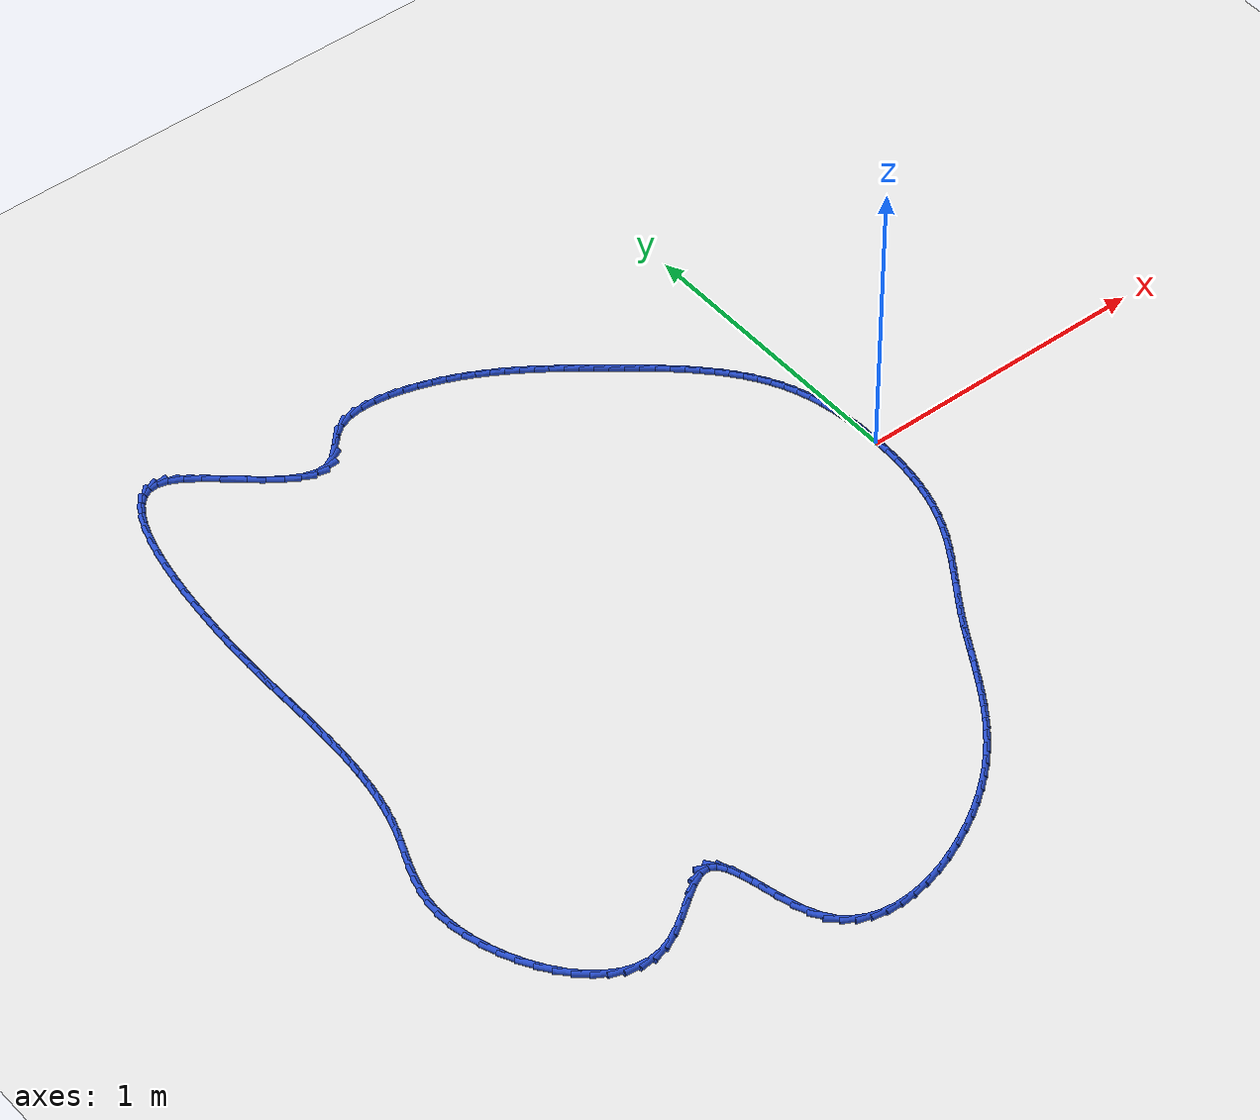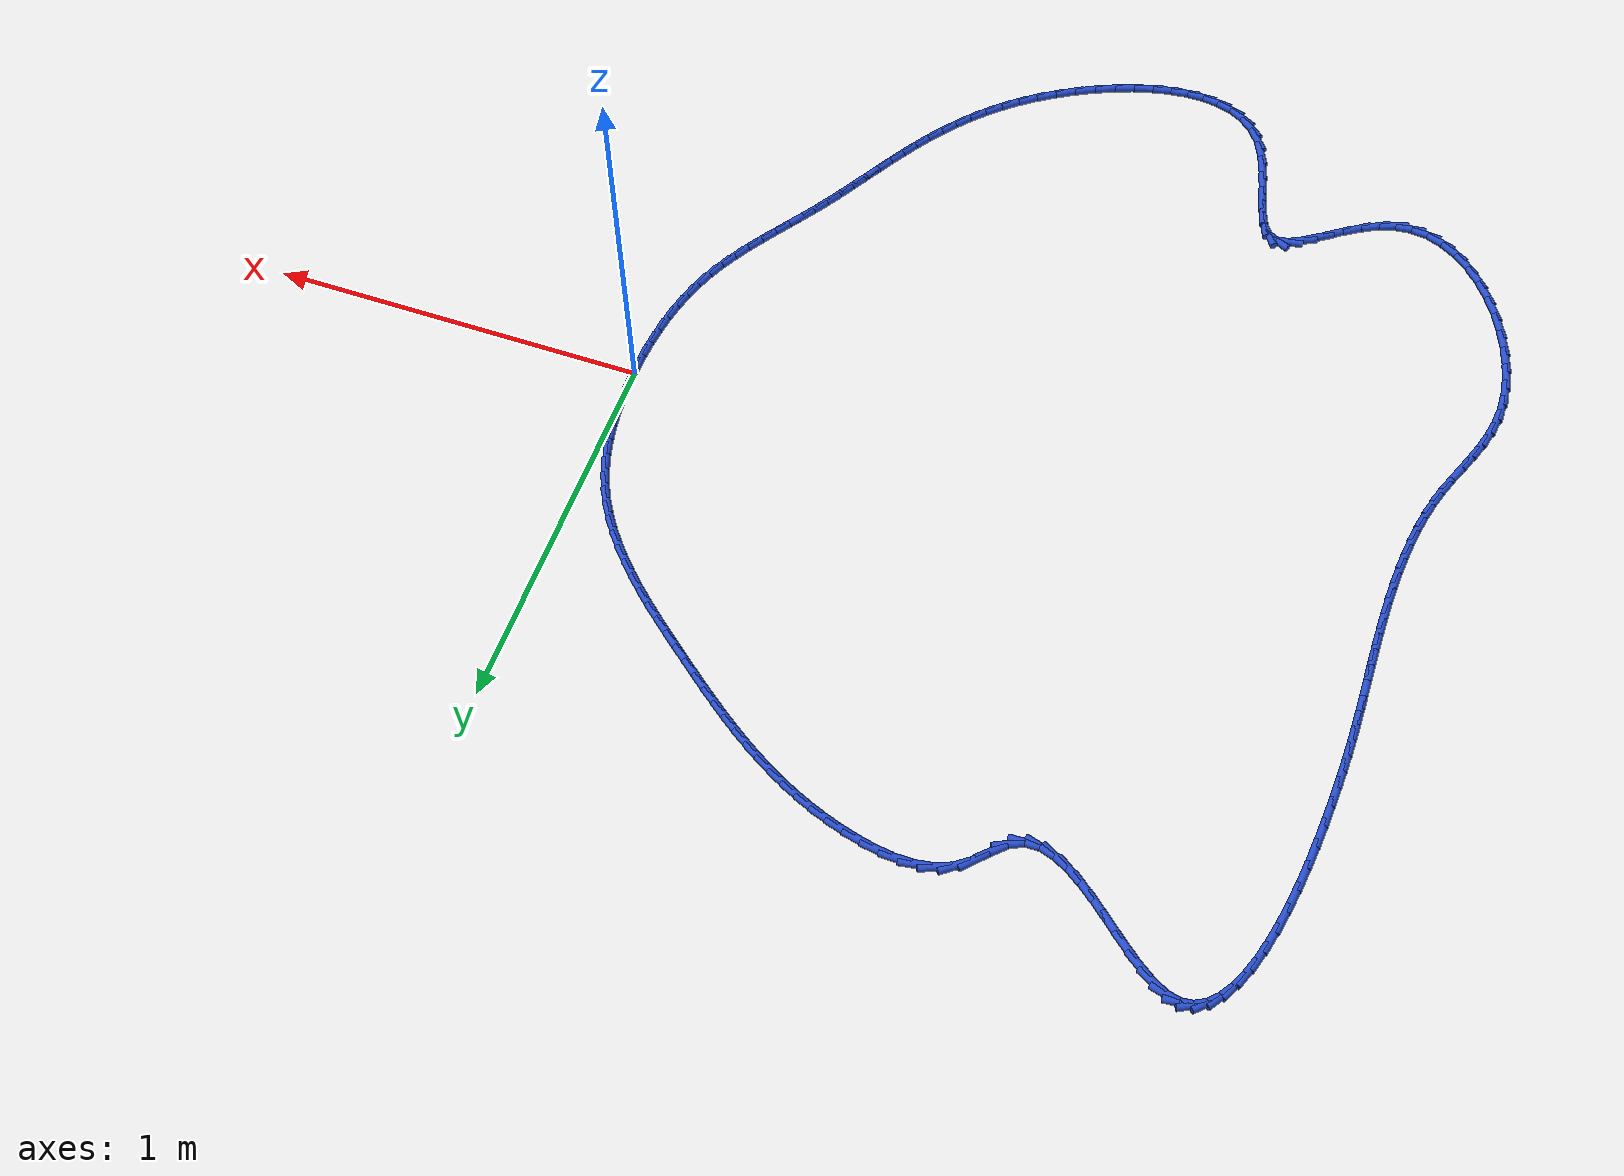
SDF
<sdf version="1.6">
 <world name="default">
  <light name="sun" type="directional">
   <pose>0 0 10 0 -0 0</pose>
   <diffuse>0.8 0.8 0.8 1</diffuse>
   <specular>0.2 0.2 0.2 1</specular>
   <attenuation>
    <range>1000</range>
    <constant>0.9</constant>
    <linear>0.01</linear>
    <quadratic>0.001</quadratic>
   </attenuation>
   <direction>-0.5 0.1 -0.9</direction>
  </light>
  <model name="ground_plane">
   <static>1</static>
   <link name="link">
    <collision name="collision">
     <geometry><plane><normal>0 0 1</normal><size>100 100</size></plane></geometry>
     <surface><friction><ode><mu>100</mu><mu2>50</mu2></ode></friction></surface>
    </collision>
    <visual name="visual">
     <cast_shadows>0</cast_shadows>
     <geometry><plane><normal>0 0 1</normal><size>100 100</size></plane></geometry>
     <material>
      <script><uri>file://media/materials/scripts/gazebo.material</uri><name>Gazebo/WhiteGlow</name></script>
     </material>
    </visual>
   </link>
  </model>
  <gravity>0 0 -9.8</gravity>
  <magnetic_field>6e-06 2.3e-05 -4.2e-05</magnetic_field>
  <atmosphere type="adiabatic"/>
  <physics name="default_physics" default="0" type="ode">
   <max_step_size>0.001</max_step_size>
   <real_time_factor>1</real_time_factor>
   <real_time_update_rate>1000</real_time_update_rate>
  </physics>
  <scene><ambient>0.4 0.4 0.4 1</ambient><background>0.7 0.7 0.7 1</background><shadows>1</shadows></scene>
  <spherical_coordinates>
   <surface_model>EARTH_WGS84</surface_model>
   <latitude_deg>0</latitude_deg>
   <longitude_deg>0</longitude_deg>
   <elevation>0</elevation>
   <heading_deg>0</heading_deg>
  </spherical_coordinates>
  <model name="line">
   <link name="link_0">
    <pose>-2.2551405187698492e-17 1.5265566588595902e-16 0.01 0 1.57 -1.5581110182866578</pose>
    <collision name="collision">
     <geometry><cylinder><radius>0.01</radius><length>0.08</length></cylinder></geometry>
    </collision>
    <visual name="visual">
     <material>
      <script><name>Gazebo/Blue</name><uri>file://media/materials/scripts/gazebo.material</uri></script>
     </material>
     <geometry><cylinder><radius>0.01</radius><length>0.08</length></cylinder></geometry>
    </visual>
   </link>
   <link name="link_1">
    <pose>-0.0005864934314034655 0.04623158922415922 0.01 0 1.57 -1.5196813050333393</pose>
    <collision name="collision">
     <geometry><cylinder><radius>0.01</radius><length>0.08</length></cylinder></geometry>
    </collision>
    <visual name="visual">
     <material>
      <script><name>Gazebo/Blue</name><uri>file://media/materials/scripts/gazebo.material</uri></script>
     </material>
     <geometry><cylinder><radius>0.01</radius><length>0.08</length></cylinder></geometry>
    </visual>
   </link>
   <link name="link_2">
    <pose>-0.002946953853219973 0.09237075187400023 0.01 0 1.57 -1.4768216190914107</pose>
    <collision name="collision">
     <geometry><cylinder><radius>0.01</radius><length>0.08</length></cylinder></geometry>
    </collision>
    <visual name="visual">
     <material>
      <script><name>Gazebo/Blue</name><uri>file://media/materials/scripts/gazebo.material</uri></script>
     </material>
     <geometry><cylinder><radius>0.01</radius><length>0.08</length></cylinder></geometry>
    </visual>
   </link>
   <link name="link_3">
    <pose>-0.007266713185651544 0.13820261088529684 0.01 0 1.57 -1.4290814146857238</pose>
    <collision name="collision">
     <geometry><cylinder><radius>0.01</radius><length>0.08</length></cylinder></geometry>
    </collision>
    <visual name="visual">
     <material>
      <script><name>Gazebo/Blue</name><uri>file://media/materials/scripts/gazebo.material</uri></script>
     </material>
     <geometry><cylinder><radius>0.01</radius><length>0.08</length></cylinder></geometry>
    </visual>
   </link>
   <link name="link_4">
    <pose>-0.01373110334890018 0.18351228919382262 0.01 0 1.57 -1.3759944871478906</pose>
    <collision name="collision">
     <geometry><cylinder><radius>0.01</radius><length>0.08</length></cylinder></geometry>
    </collision>
    <visual name="visual">
     <material>
      <script><name>Gazebo/Blue</name><uri>file://media/materials/scripts/gazebo.material</uri></script>
     </material>
     <geometry><cylinder><radius>0.01</radius><length>0.08</length></cylinder></geometry>
    </visual>
   </link>
   <link name="link_5">
    <pose>-0.02252545626316788 0.2280849097353512 0.01 0 1.57 -1.3171097519300026</pose>
    <collision name="collision">
     <geometry><cylinder><radius>0.01</radius><length>0.08</length></cylinder></geometry>
    </collision>
    <visual name="visual">
     <material>
      <script><name>Gazebo/Blue</name><uri>file://media/materials/scripts/gazebo.material</uri></script>
     </material>
     <geometry><cylinder><radius>0.01</radius><length>0.08</length></cylinder></geometry>
    </visual>
   </link>
   <link name="link_6">
    <pose>-0.03383510384865665 0.27170559544565603 0.01 0 1.57 -1.2520382343686818</pose>
    <collision name="collision">
     <geometry><cylinder><radius>0.01</radius><length>0.08</length></cylinder></geometry>
    </collision>
    <visual name="visual">
     <material>
      <script><name>Gazebo/Blue</name><uri>file://media/materials/scripts/gazebo.material</uri></script>
     </material>
     <geometry><cylinder><radius>0.01</radius><length>0.08</length></cylinder></geometry>
    </visual>
   </link>
   <link name="link_7">
    <pose>-0.047845378025568486 0.3141594692605107 0.01 0 1.57 -1.1805191520707605</pose>
    <collision name="collision">
     <geometry><cylinder><radius>0.01</radius><length>0.08</length></cylinder></geometry>
    </collision>
    <visual name="visual">
     <material>
      <script><name>Gazebo/Blue</name><uri>file://media/materials/scripts/gazebo.material</uri></script>
     </material>
     <geometry><cylinder><radius>0.01</radius><length>0.08</length></cylinder></geometry>
    </visual>
   </link>
   <link name="link_8">
    <pose>-0.06474161071410542 0.355231654115689 0.01 0 1.57 -1.103817215434472</pose>
    <collision name="collision">
     <geometry><cylinder><radius>0.01</radius><length>0.08</length></cylinder></geometry>
    </collision>
    <visual name="visual">
     <material>
      <script><name>Gazebo/Blue</name><uri>file://media/materials/scripts/gazebo.material</uri></script>
     </material>
     <geometry><cylinder><radius>0.01</radius><length>0.08</length></cylinder></geometry>
    </visual>
   </link>
   <link name="link_9">
    <pose>-0.08466116027922482 0.3947411381217055 0.01 0 1.57 -1.0305617225246773</pose>
    <collision name="collision">
     <geometry><cylinder><radius>0.01</radius><length>0.08</length></cylinder></geometry>
    </collision>
    <visual name="visual">
     <material>
      <script><name>Gazebo/Blue</name><uri>file://media/materials/scripts/gazebo.material</uri></script>
     </material>
     <geometry><cylinder><radius>0.01</radius><length>0.08</length></cylinder></geometry>
    </visual>
   </link>
   <link name="link_10">
    <pose>-0.10743910433282212 0.4327202934184871 0.01 0 1.57 -0.9645054290978226</pose>
    <collision name="collision">
     <geometry><cylinder><radius>0.01</radius><length>0.08</length></cylinder></geometry>
    </collision>
    <visual name="visual">
     <material>
      <script><name>Gazebo/Blue</name><uri>file://media/materials/scripts/gazebo.material</uri></script>
     </material>
     <geometry><cylinder><radius>0.01</radius><length>0.08</length></cylinder></geometry>
    </visual>
   </link>
   <link name="link_11">
    <pose>-0.1327930913785158 0.4692843869252037 0.01 0 1.57 -0.9058867984979098</pose>
    <collision name="collision">
     <geometry><cylinder><radius>0.01</radius><length>0.08</length></cylinder></geometry>
    </collision>
    <visual name="visual">
     <material>
      <script><name>Gazebo/Blue</name><uri>file://media/materials/scripts/gazebo.material</uri></script>
     </material>
     <geometry><cylinder><radius>0.01</radius><length>0.08</length></cylinder></geometry>
    </visual>
   </link>
   <link name="link_12">
    <pose>-0.1604405091065469 0.5045488696726791 0.01 0 1.57 -0.854665689048277</pose>
    <collision name="collision">
     <geometry><cylinder><radius>0.01</radius><length>0.08</length></cylinder></geometry>
    </collision>
    <visual name="visual">
     <material>
      <script><name>Gazebo/Blue</name><uri>file://media/materials/scripts/gazebo.material</uri></script>
     </material>
     <geometry><cylinder><radius>0.01</radius><length>0.08</length></cylinder></geometry>
    </visual>
   </link>
   <link name="link_13">
    <pose>-0.19009874520715628 0.538629192691737 0.01 0 1.57 -0.8106291621072089</pose>
    <collision name="collision">
     <geometry><cylinder><radius>0.01</radius><length>0.08</length></cylinder></geometry>
    </collision>
    <visual name="visual">
     <material>
      <script><name>Gazebo/Blue</name><uri>file://media/materials/scripts/gazebo.material</uri></script>
     </material>
     <geometry><cylinder><radius>0.01</radius><length>0.08</length></cylinder></geometry>
    </visual>
   </link>
   <link name="link_14">
    <pose>-0.22148518737058487 0.5716408070132014 0.01 0 1.57 -0.7734758652950425</pose>
    <collision name="collision">
     <geometry><cylinder><radius>0.01</radius><length>0.08</length></cylinder></geometry>
    </collision>
    <visual name="visual">
     <material>
      <script><name>Gazebo/Blue</name><uri>file://media/materials/scripts/gazebo.material</uri></script>
     </material>
     <geometry><cylinder><radius>0.01</radius><length>0.08</length></cylinder></geometry>
    </visual>
   </link>
   <link name="link_15">
    <pose>-0.25431722328707346 0.603699163667896 0.01 0 1.57 -0.7428807795332064</pose>
    <collision name="collision">
     <geometry><cylinder><radius>0.01</radius><length>0.08</length></cylinder></geometry>
    </collision>
    <visual name="visual">
     <material>
      <script><name>Gazebo/Blue</name><uri>file://media/materials/scripts/gazebo.material</uri></script>
     </material>
     <geometry><cylinder><radius>0.01</radius><length>0.08</length></cylinder></geometry>
    </visual>
   </link>
   <link name="link_16">
    <pose>-0.2883122406468632 0.6349197136866445 0.01 0 1.57 -0.7185413642997761</pose>
    <collision name="collision">
     <geometry><cylinder><radius>0.01</radius><length>0.08</length></cylinder></geometry>
    </collision>
    <visual name="visual">
     <material>
      <script><name>Gazebo/Blue</name><uri>file://media/materials/scripts/gazebo.material</uri></script>
     </material>
     <geometry><cylinder><radius>0.01</radius><length>0.08</length></cylinder></geometry>
    </visual>
   </link>
   <link name="link_17">
    <pose>-0.323187627140195 0.6654179081002709 0.01 0 1.57 -0.7002089588902889</pose>
    <collision name="collision">
     <geometry><cylinder><radius>0.01</radius><length>0.08</length></cylinder></geometry>
    </collision>
    <visual name="visual">
     <material>
      <script><name>Gazebo/Blue</name><uri>file://media/materials/scripts/gazebo.material</uri></script>
     </material>
     <geometry><cylinder><radius>0.01</radius><length>0.08</length></cylinder></geometry>
    </visual>
   </link>
   <link name="link_18">
    <pose>-0.3586607704573096 0.6953091979395991 0.01 0 1.57 -0.6877098649833832</pose>
    <collision name="collision">
     <geometry><cylinder><radius>0.01</radius><length>0.08</length></cylinder></geometry>
    </collision>
    <visual name="visual">
     <material>
      <script><name>Gazebo/Blue</name><uri>file://media/materials/scripts/gazebo.material</uri></script>
     </material>
     <geometry><cylinder><radius>0.01</radius><length>0.08</length></cylinder></geometry>
    </visual>
   </link>
   <link name="link_19">
    <pose>-0.394449058288448 0.7247090342354525 0.01 0 1.57 -0.6809553234066922</pose>
    <collision name="collision">
     <geometry><cylinder><radius>0.01</radius><length>0.08</length></cylinder></geometry>
    </collision>
    <visual name="visual">
     <material>
      <script><name>Gazebo/Blue</name><uri>file://media/materials/scripts/gazebo.material</uri></script>
     </material>
     <geometry><cylinder><radius>0.01</radius><length>0.08</length></cylinder></geometry>
    </visual>
   </link>
   <link name="link_20">
    <pose>-0.43027007798238903 0.7537327517395714 0.01 0 1.57 -0.6774845087517437</pose>
    <collision name="collision">
     <geometry><cylinder><radius>0.01</radius><length>0.08</length></cylinder></geometry>
    </collision>
    <visual name="visual">
     <material>
      <script><name>Gazebo/Blue</name><uri>file://media/materials/scripts/gazebo.material</uri></script>
     </material>
     <geometry><cylinder><radius>0.01</radius><length>0.08</length></cylinder></geometry>
    </visual>
   </link>
   <link name="link_21">
    <pose>-0.4659462972252049 0.7824346039713038 0.01 0 1.57 -0.6707703880572167</pose>
    <collision name="collision">
     <geometry><cylinder><radius>0.01</radius><length>0.08</length></cylinder></geometry>
    </collision>
    <visual name="visual">
     <material>
      <script><name>Gazebo/Blue</name><uri>file://media/materials/scripts/gazebo.material</uri></script>
     </material>
     <geometry><cylinder><radius>0.01</radius><length>0.08</length></cylinder></geometry>
    </visual>
   </link>
   <link name="link_22">
    <pose>-0.5015768158342331 0.8107077367349306 0.01 0 1.57 -0.6596830556676785</pose>
    <collision name="collision">
     <geometry><cylinder><radius>0.01</radius><length>0.08</length></cylinder></geometry>
    </collision>
    <visual name="visual">
     <material>
      <script><name>Gazebo/Blue</name><uri>file://media/materials/scripts/gazebo.material</uri></script>
     </material>
     <geometry><cylinder><radius>0.01</radius><length>0.08</length></cylinder></geometry>
    </visual>
   </link>
   <link name="link_23">
    <pose>-0.5373058098281287 0.8384190439175578 0.01 0 1.57 -0.6441704811285792</pose>
    <collision name="collision">
     <geometry><cylinder><radius>0.01</radius><length>0.08</length></cylinder></geometry>
    </collision>
    <visual name="visual">
     <material>
      <script><name>Gazebo/Blue</name><uri>file://media/materials/scripts/gazebo.material</uri></script>
     </material>
     <geometry><cylinder><radius>0.01</radius><length>0.08</length></cylinder></geometry>
    </visual>
   </link>
   <link name="link_24">
    <pose>-0.5732774552255456 0.8654354194062905 0.01 0 1.57 -0.6242084631560192</pose>
    <collision name="collision">
     <geometry><cylinder><radius>0.01</radius><length>0.08</length></cylinder></geometry>
    </collision>
    <visual name="visual">
     <material>
      <script><name>Gazebo/Blue</name><uri>file://media/materials/scripts/gazebo.material</uri></script>
     </material>
     <geometry><cylinder><radius>0.01</radius><length>0.08</length></cylinder></geometry>
    </visual>
   </link>
   <link name="link_25">
    <pose>-0.6096359280451388 0.8916237570882347 0.01 0 1.57 -0.5998106167229476</pose>
    <collision name="collision">
     <geometry><cylinder><radius>0.01</radius><length>0.08</length></cylinder></geometry>
    </collision>
    <visual name="visual">
     <material>
      <script><name>Gazebo/Blue</name><uri>file://media/materials/scripts/gazebo.material</uri></script>
     </material>
     <geometry><cylinder><radius>0.01</radius><length>0.08</length></cylinder></geometry>
    </visual>
   </link>
   <link name="link_26">
    <pose>-0.6465254043055628 0.9168509508504957 0.01 0 1.57 -0.5710404959013357</pose>
    <collision name="collision">
     <geometry><cylinder><radius>0.01</radius><length>0.08</length></cylinder></geometry>
    </collision>
    <visual name="visual">
     <material>
      <script><name>Gazebo/Blue</name><uri>file://media/materials/scripts/gazebo.material</uri></script>
     </material>
     <geometry><cylinder><radius>0.01</radius><length>0.08</length></cylinder></geometry>
    </visual>
   </link>
   <link name="link_27">
    <pose>-0.6840900600254719 0.9409838945801787 0.01 0 1.57 -0.5380250017368592</pose>
    <collision name="collision">
     <geometry><cylinder><radius>0.01</radius><length>0.08</length></cylinder></geometry>
    </collision>
    <visual name="visual">
     <material>
      <script><name>Gazebo/Blue</name><uri>file://media/materials/scripts/gazebo.material</uri></script>
     </material>
     <geometry><cylinder><radius>0.01</radius><length>0.08</length></cylinder></geometry>
    </visual>
   </link>
   <link name="link_28">
    <pose>-0.7224740712235211 0.96388948216439 0.01 0 1.57 -0.500967664206688</pose>
    <collision name="collision">
     <geometry><cylinder><radius>0.01</radius><length>0.08</length></cylinder></geometry>
    </collision>
    <visual name="visual">
     <material>
      <script><name>Gazebo/Blue</name><uri>file://media/materials/scripts/gazebo.material</uri></script>
     </material>
     <geometry><cylinder><radius>0.01</radius><length>0.08</length></cylinder></geometry>
    </visual>
   </link>
   <link name="link_29">
    <pose>-0.761821613918365 0.9854346074902346 0.01 0 1.57 -0.46015981484920965</pose>
    <collision name="collision">
     <geometry><cylinder><radius>0.01</radius><length>0.08</length></cylinder></geometry>
    </collision>
    <visual name="visual">
     <material>
      <script><name>Gazebo/Blue</name><uri>file://media/materials/scripts/gazebo.material</uri></script>
     </material>
     <geometry><cylinder><radius>0.01</radius><length>0.08</length></cylinder></geometry>
    </visual>
   </link>
   <link name="link_30">
    <pose>-0.8022768641286578 1.005486164444818 0.01 0 1.57 -0.4159872505350488</pose>
    <collision name="collision">
     <geometry><cylinder><radius>0.01</radius><length>0.08</length></cylinder></geometry>
    </collision>
    <visual name="visual">
     <material>
      <script><name>Gazebo/Blue</name><uri>file://media/materials/scripts/gazebo.material</uri></script>
     </material>
     <geometry><cylinder><radius>0.01</radius><length>0.08</length></cylinder></geometry>
    </visual>
   </link>
   <link name="link_31">
    <pose>-0.8439839978730546 1.0239110469152464 0.01 0 1.57 -0.36892995409020823</pose>
    <collision name="collision">
     <geometry><cylinder><radius>0.01</radius><length>0.08</length></cylinder></geometry>
    </collision>
    <visual name="visual">
     <material>
      <script><name>Gazebo/Blue</name><uri>file://media/materials/scripts/gazebo.material</uri></script>
     </material>
     <geometry><cylinder><radius>0.01</radius><length>0.08</length></cylinder></geometry>
    </visual>
   </link>
   <link name="link_32">
    <pose>-0.8870871911702094 1.0405761487886245 0.01 0 1.57 -0.31955299316979413</pose>
    <collision name="collision">
     <geometry><cylinder><radius>0.01</radius><length>0.08</length></cylinder></geometry>
    </collision>
    <visual name="visual">
     <material>
      <script><name>Gazebo/Blue</name><uri>file://media/materials/scripts/gazebo.material</uri></script>
     </material>
     <geometry><cylinder><radius>0.01</radius><length>0.08</length></cylinder></geometry>
    </visual>
   </link>
   <link name="link_33">
    <pose>-0.9317306200387776 1.0553483639520587 0.01 0 1.57 -0.2684605193509171</pose>
    <collision name="collision">
     <geometry><cylinder><radius>0.01</radius><length>0.08</length></cylinder></geometry>
    </collision>
    <visual name="visual">
     <material>
      <script><name>Gazebo/Blue</name><uri>file://media/materials/scripts/gazebo.material</uri></script>
     </material>
     <geometry><cylinder><radius>0.01</radius><length>0.08</length></cylinder></geometry>
    </visual>
   </link>
   <link name="link_34">
    <pose>-0.978056793665534 1.0680927611725068 0.01 0 1.57 -0.2094258496542681</pose>
    <collision name="collision">
     <geometry><cylinder><radius>0.01</radius><length>0.08</length></cylinder></geometry>
    </collision>
    <visual name="visual">
     <material>
      <script><name>Gazebo/Blue</name><uri>file://media/materials/scripts/gazebo.material</uri></script>
     </material>
     <geometry><cylinder><radius>0.01</radius><length>0.08</length></cylinder></geometry>
    </visual>
   </link>
   <link name="link_35">
    <pose>-1.0258144935837161 1.078243291788705 0.01 0 1.57 -0.12437987758433425</pose>
    <collision name="collision">
     <geometry><cylinder><radius>0.01</radius><length>0.08</length></cylinder></geometry>
    </collision>
    <visual name="visual">
     <material>
      <script><name>Gazebo/Blue</name><uri>file://media/materials/scripts/gazebo.material</uri></script>
     </material>
     <geometry><cylinder><radius>0.01</radius><length>0.08</length></cylinder></geometry>
    </visual>
   </link>
   <link name="link_36">
    <pose>-1.0738533434648931 1.084249362057518 0.01 0 1.57 -0.0037031809191358264</pose>
    <collision name="collision">
     <geometry><cylinder><radius>0.01</radius><length>0.08</length></cylinder></geometry>
    </collision>
    <visual name="visual">
     <material>
      <script><name>Gazebo/Blue</name><uri>file://media/materials/scripts/gazebo.material</uri></script>
     </material>
     <geometry><cylinder><radius>0.01</radius><length>0.08</length></cylinder></geometry>
    </visual>
   </link>
   <link name="link_37">
    <pose>-1.1208980309558838 1.0844235778429543 0.01 0 1.57 0.1625942439429418</pose>
    <collision name="collision">
     <geometry><cylinder><radius>0.01</radius><length>0.08</length></cylinder></geometry>
    </collision>
    <visual name="visual">
     <material>
      <script><name>Gazebo/Blue</name><uri>file://media/materials/scripts/gazebo.material</uri></script>
     </material>
     <geometry><cylinder><radius>0.01</radius><length>0.08</length></cylinder></geometry>
    </visual>
   </link>
   <link name="link_38">
    <pose>-1.1656732437035078 1.0770785450090217 0.01 0 1.57 0.38174992853129747</pose>
    <collision name="collision">
     <geometry><cylinder><radius>0.01</radius><length>0.08</length></cylinder></geometry>
    </collision>
    <visual name="visual">
     <material>
      <script><name>Gazebo/Blue</name><uri>file://media/materials/scripts/gazebo.material</uri></script>
     </material>
     <geometry><cylinder><radius>0.01</radius><length>0.08</length></cylinder></geometry>
    </visual>
   </link>
   <link name="link_39">
    <pose>-1.2069036693545856 1.0605268694197296 0.01 0 1.57 0.6428385513464456</pose>
    <collision name="collision">
     <geometry><cylinder><radius>0.01</radius><length>0.08</length></cylinder></geometry>
    </collision>
    <visual name="visual">
     <material>
      <script><name>Gazebo/Blue</name><uri>file://media/materials/scripts/gazebo.material</uri></script>
     </material>
     <geometry><cylinder><radius>0.01</radius><length>0.08</length></cylinder></geometry>
    </visual>
   </link>
   <link name="link_40">
    <pose>-1.2433641772313597 1.0332192153658406 0.01 0 1.57 0.8137842402079073</pose>
    <collision name="collision">
     <geometry><cylinder><radius>0.01</radius><length>0.08</length></cylinder></geometry>
    </collision>
    <visual name="visual">
     <material>
      <script><name>Gazebo/Blue</name><uri>file://media/materials/scripts/gazebo.material</uri></script>
     </material>
     <geometry><cylinder><radius>0.01</radius><length>0.08</length></cylinder></geometry>
    </visual>
   </link>
   <link name="link_41">
    <pose>-1.2757633985514543 0.9989263589665922 0.01 0 1.57 0.7705133797748409</pose>
    <collision name="collision">
     <geometry><cylinder><radius>0.01</radius><length>0.08</length></cylinder></geometry>
    </collision>
    <visual name="visual">
     <material>
      <script><name>Gazebo/Blue</name><uri>file://media/materials/scripts/gazebo.material</uri></script>
     </material>
     <geometry><cylinder><radius>0.01</radius><length>0.08</length></cylinder></geometry>
    </visual>
   </link>
   <link name="link_42">
    <pose>-1.3073121697854584 0.9683030736913412 0.01 0 1.57 0.46118947887092043</pose>
    <collision name="collision">
     <geometry><cylinder><radius>0.01</radius><length>0.08</length></cylinder></geometry>
    </collision>
    <visual name="visual">
     <material>
      <script><name>Gazebo/Blue</name><uri>file://media/materials/scripts/gazebo.material</uri></script>
     </material>
     <geometry><cylinder><radius>0.01</radius><length>0.08</length></cylinder></geometry>
    </visual>
   </link>
   <link name="link_43">
    <pose>-1.3411124056794164 0.9515066851858648 0.01 0 1.57 0.03333369516429722</pose>
    <collision name="collision">
     <geometry><cylinder><radius>0.01</radius><length>0.08</length></cylinder></geometry>
    </collision>
    <visual name="visual">
     <material>
      <script><name>Gazebo/Blue</name><uri>file://media/materials/scripts/gazebo.material</uri></script>
     </material>
     <geometry><cylinder><radius>0.01</radius><length>0.08</length></cylinder></geometry>
    </visual>
   </link>
   <link name="link_44">
    <pose>-1.3778416122851653 0.9502819113458469 0.01 0 1.57 -0.291311463790889</pose>
    <collision name="collision">
     <geometry><cylinder><radius>0.01</radius><length>0.08</length></cylinder></geometry>
    </collision>
    <visual name="visual">
     <material>
      <script><name>Gazebo/Blue</name><uri>file://media/materials/scripts/gazebo.material</uri></script>
     </material>
     <geometry><cylinder><radius>0.01</radius><length>0.08</length></cylinder></geometry>
    </visual>
   </link>
   <link name="link_45">
    <pose>-1.4169163838821284 0.9619981532426475 0.01 0 1.57 -0.49405290184933237</pose>
    <collision name="collision">
     <geometry><cylinder><radius>0.01</radius><length>0.08</length></cylinder></geometry>
    </collision>
    <visual name="visual">
     <material>
      <script><name>Gazebo/Blue</name><uri>file://media/materials/scripts/gazebo.material</uri></script>
     </material>
     <geometry><cylinder><radius>0.01</radius><length>0.08</length></cylinder></geometry>
    </visual>
   </link>
   <link name="link_46">
    <pose>-1.4577425120795617 0.983987327085045 0.01 0 1.57 -0.6140071566286842</pose>
    <collision name="collision">
     <geometry><cylinder><radius>0.01</radius><length>0.08</length></cylinder></geometry>
    </collision>
    <visual name="visual">
     <material>
      <script><name>Gazebo/Blue</name><uri>file://media/materials/scripts/gazebo.material</uri></script>
     </material>
     <geometry><cylinder><radius>0.01</radius><length>0.08</length></cylinder></geometry>
    </visual>
   </link>
   <link name="link_47">
    <pose>-1.4997257884867254 1.0135813490818188 0.01 0 1.57 -0.6817781273284622</pose>
    <collision name="collision">
     <geometry><cylinder><radius>0.01</radius><length>0.08</length></cylinder></geometry>
    </collision>
    <visual name="visual">
     <material>
      <script><name>Gazebo/Blue</name><uri>file://media/materials/scripts/gazebo.material</uri></script>
     </material>
     <geometry><cylinder><radius>0.01</radius><length>0.08</length></cylinder></geometry>
    </visual>
   </link>
   <link name="link_48">
    <pose>-1.5422720047128755 1.0481121354417469 0.01 0 1.57 -0.7134614498351695</pose>
    <collision name="collision">
     <geometry><cylinder><radius>0.01</radius><length>0.08</length></cylinder></geometry>
    </collision>
    <visual name="visual">
     <material>
      <script><name>Gazebo/Blue</name><uri>file://media/materials/scripts/gazebo.material</uri></script>
     </material>
     <geometry><cylinder><radius>0.01</radius><length>0.08</length></cylinder></geometry>
    </visual>
   </link>
   <link name="link_49">
    <pose>-1.5847869523672717 1.0849116023736094 0.01 0 1.57 -0.7153959912994973</pose>
    <collision name="collision">
     <geometry><cylinder><radius>0.01</radius><length>0.08</length></cylinder></geometry>
    </collision>
    <visual name="visual">
     <material>
      <script><name>Gazebo/Blue</name><uri>file://media/materials/scripts/gazebo.material</uri></script>
     </material>
     <geometry><cylinder><radius>0.01</radius><length>0.08</length></cylinder></geometry>
    </visual>
   </link>
   <link name="link_50">
    <pose>-1.6266764230591717 1.1213116660861844 0.01 0 1.57 -0.6865728458803131</pose>
    <collision name="collision">
     <geometry><cylinder><radius>0.01</radius><length>0.08</length></cylinder></geometry>
    </collision>
    <visual name="visual">
     <material>
      <script><name>Gazebo/Blue</name><uri>file://media/materials/scripts/gazebo.material</uri></script>
     </material>
     <geometry><cylinder><radius>0.01</radius><length>0.08</length></cylinder></geometry>
    </visual>
   </link>
   <link name="link_51">
    <pose>-1.6673462083978334 1.1546442427882504 0.01 0 1.57 -0.6175653939823988</pose>
    <collision name="collision">
     <geometry><cylinder><radius>0.01</radius><length>0.08</length></cylinder></geometry>
    </collision>
    <visual name="visual">
     <material>
      <script><name>Gazebo/Blue</name><uri>file://media/materials/scripts/gazebo.material</uri></script>
     </material>
     <geometry><cylinder><radius>0.01</radius><length>0.08</length></cylinder></geometry>
    </visual>
   </link>
   <link name="link_52">
    <pose>-1.7062020999925156 1.1822412486885876 0.01 0 1.57 -0.48469928933581025</pose>
    <collision name="collision">
     <geometry><cylinder><radius>0.01</radius><length>0.08</length></cylinder></geometry>
    </collision>
    <visual name="visual">
     <material>
      <script><name>Gazebo/Blue</name><uri>file://media/materials/scripts/gazebo.material</uri></script>
     </material>
     <geometry><cylinder><radius>0.01</radius><length>0.08</length></cylinder></geometry>
    </visual>
   </link>
   <link name="link_53">
    <pose>-1.7426498894524758 1.2014345999959737 0.01 0 1.57 -0.24039862072239954</pose>
    <collision name="collision">
     <geometry><cylinder><radius>0.01</radius><length>0.08</length></cylinder></geometry>
    </collision>
    <visual name="visual">
     <material>
      <script><name>Gazebo/Blue</name><uri>file://media/materials/scripts/gazebo.material</uri></script>
     </material>
     <geometry><cylinder><radius>0.01</radius><length>0.08</length></cylinder></geometry>
    </visual>
   </link>
   <link name="link_54">
    <pose>-1.7761115640180518 1.2096373693537716 0.01 0 1.57 0.11667656935123075</pose>
    <collision name="collision">
     <geometry><cylinder><radius>0.01</radius><length>0.08</length></cylinder></geometry>
    </collision>
    <visual name="visual">
     <material>
      <script><name>Gazebo/Blue</name><uri>file://media/materials/scripts/gazebo.material</uri></script>
     </material>
     <geometry><cylinder><radius>0.01</radius><length>0.08</length></cylinder></geometry>
    </visual>
   </link>
   <link name="link_55">
    <pose>-1.8063738538254013 1.206090358921826 0.01 0 1.57 0.48241739537349754</pose>
    <collision name="collision">
     <geometry><cylinder><radius>0.01</radius><length>0.08</length></cylinder></geometry>
    </collision>
    <visual name="visual">
     <material>
      <script><name>Gazebo/Blue</name><uri>file://media/materials/scripts/gazebo.material</uri></script>
     </material>
     <geometry><cylinder><radius>0.01</radius><length>0.08</length></cylinder></geometry>
    </visual>
   </link>
   <link name="link_56">
    <pose>-1.8335839740180322 1.1918407640639377 0.01 0 1.57 0.7751715401620098</pose>
    <collision name="collision">
     <geometry><cylinder><radius>0.01</radius><length>0.08</length></cylinder></geometry>
    </collision>
    <visual name="visual">
     <material>
      <script><name>Gazebo/Blue</name><uri>file://media/materials/scripts/gazebo.material</uri></script>
     </material>
     <geometry><cylinder><radius>0.01</radius><length>0.08</length></cylinder></geometry>
    </visual>
   </link>
   <link name="link_57">
    <pose>-1.8579044837560361 1.1680126691315373 0.01 0 1.57 0.9812558598755927</pose>
    <collision name="collision">
     <geometry><cylinder><radius>0.01</radius><length>0.08</length></cylinder></geometry>
    </collision>
    <visual name="visual">
     <material>
      <script><name>Gazebo/Blue</name><uri>file://media/materials/scripts/gazebo.material</uri></script>
     </material>
     <geometry><cylinder><radius>0.01</radius><length>0.08</length></cylinder></geometry>
    </visual>
   </link>
   <link name="link_58">
    <pose>-1.879497942199505 1.1357301584760566 0.01 0 1.57 1.1229726978186385</pose>
    <collision name="collision">
     <geometry><cylinder><radius>0.01</radius><length>0.08</length></cylinder></geometry>
    </collision>
    <visual name="visual">
     <material>
      <script><name>Gazebo/Blue</name><uri>file://media/materials/scripts/gazebo.material</uri></script>
     </material>
     <geometry><cylinder><radius>0.01</radius><length>0.08</length></cylinder></geometry>
    </visual>
   </link>
   <link name="link_59">
    <pose>-1.8985269085085288 1.0961173164489282 0.01 0 1.57 1.2226896131673166</pose>
    <collision name="collision">
     <geometry><cylinder><radius>0.01</radius><length>0.08</length></cylinder></geometry>
    </collision>
    <visual name="visual">
     <material>
      <script><name>Gazebo/Blue</name><uri>file://media/materials/scripts/gazebo.material</uri></script>
     </material>
     <geometry><cylinder><radius>0.01</radius><length>0.08</length></cylinder></geometry>
    </visual>
   </link>
   <link name="link_60">
    <pose>-1.9151539418431982 1.0502982274015817 0.01 0 1.57 1.2953243200893407</pose>
    <collision name="collision">
     <geometry><cylinder><radius>0.01</radius><length>0.08</length></cylinder></geometry>
    </collision>
    <visual name="visual">
     <material>
      <script><name>Gazebo/Blue</name><uri>file://media/materials/scripts/gazebo.material</uri></script>
     </material>
     <geometry><cylinder><radius>0.01</radius><length>0.08</length></cylinder></geometry>
    </visual>
   </link>
   <link name="link_61">
    <pose>-1.9295416013636042 0.9993969756854494 0.01 0 1.57 1.3500459101198456</pose>
    <collision name="collision">
     <geometry><cylinder><radius>0.01</radius><length>0.08</length></cylinder></geometry>
    </collision>
    <visual name="visual">
     <material>
      <script><name>Gazebo/Blue</name><uri>file://media/materials/scripts/gazebo.material</uri></script>
     </material>
     <geometry><cylinder><radius>0.01</radius><length>0.08</length></cylinder></geometry>
    </visual>
   </link>
   <link name="link_62">
    <pose>-1.941852446229838 0.9445376456519631 0.01 0 1.57 1.392505434908142</pose>
    <collision name="collision">
     <geometry><cylinder><radius>0.01</radius><length>0.08</length></cylinder></geometry>
    </collision>
    <visual name="visual">
     <material>
      <script><name>Gazebo/Blue</name><uri>file://media/materials/scripts/gazebo.material</uri></script>
     </material>
     <geometry><cylinder><radius>0.01</radius><length>0.08</length></cylinder></geometry>
    </visual>
   </link>
   <link name="link_63">
    <pose>-1.9522490356019897 0.8868443216525531 0.01 0 1.57 1.4262818396620163</pose>
    <collision name="collision">
     <geometry><cylinder><radius>0.01</radius><length>0.08</length></cylinder></geometry>
    </collision>
    <visual name="visual">
     <material>
      <script><name>Gazebo/Blue</name><uri>file://media/materials/scripts/gazebo.material</uri></script>
     </material>
     <geometry><cylinder><radius>0.01</radius><length>0.08</length></cylinder></geometry>
    </visual>
   </link>
   <link name="link_64">
    <pose>-1.9608939286401508 0.8274410880386525 0.01 0 1.57 1.4537168571236707</pose>
    <collision name="collision">
     <geometry><cylinder><radius>0.01</radius><length>0.08</length></cylinder></geometry>
    </collision>
    <visual name="visual">
     <material>
      <script><name>Gazebo/Blue</name><uri>file://media/materials/scripts/gazebo.material</uri></script>
     </material>
     <geometry><cylinder><radius>0.01</radius><length>0.08</length></cylinder></geometry>
    </visual>
   </link>
   <link name="link_65">
    <pose>-1.9679496845044115 0.7674520291616914 0.01 0 1.57 1.4763914577113066</pose>
    <collision name="collision">
     <geometry><cylinder><radius>0.01</radius><length>0.08</length></cylinder></geometry>
    </collision>
    <visual name="visual">
     <material>
      <script><name>Gazebo/Blue</name><uri>file://media/materials/scripts/gazebo.material</uri></script>
     </material>
     <geometry><cylinder><radius>0.01</radius><length>0.08</length></cylinder></geometry>
    </visual>
   </link>
   <link name="link_66">
    <pose>-1.9735788623548638 0.7080012293731015 0.01 0 1.57 1.4954026355419876</pose>
    <collision name="collision">
     <geometry><cylinder><radius>0.01</radius><length>0.08</length></cylinder></geometry>
    </collision>
    <visual name="visual">
     <material>
      <script><name>Gazebo/Blue</name><uri>file://media/materials/scripts/gazebo.material</uri></script>
     </material>
     <geometry><cylinder><radius>0.01</radius><length>0.08</length></cylinder></geometry>
    </visual>
   </link>
   <link name="link_67">
    <pose>-1.9779440213515977 0.6502127730243149 0.01 0 1.57 1.511528023546924</pose>
    <collision name="collision">
     <geometry><cylinder><radius>0.01</radius><length>0.08</length></cylinder></geometry>
    </collision>
    <visual name="visual">
     <material>
      <script><name>Gazebo/Blue</name><uri>file://media/materials/scripts/gazebo.material</uri></script>
     </material>
     <geometry><cylinder><radius>0.01</radius><length>0.08</length></cylinder></geometry>
    </visual>
   </link>
   <link name="link_68">
    <pose>-1.9812077206547034 0.5952107444667618 0.01 0 1.57 1.52533315946196</pose>
    <collision name="collision">
     <geometry><cylinder><radius>0.01</radius><length>0.08</length></cylinder></geometry>
    </collision>
    <visual name="visual">
     <material>
      <script><name>Gazebo/Blue</name><uri>file://media/materials/scripts/gazebo.material</uri></script>
     </material>
     <geometry><cylinder><radius>0.01</radius><length>0.08</length></cylinder></geometry>
    </visual>
   </link>
   <link name="link_69">
    <pose>-1.9835323600882102 0.5441136091307579 0.01 0 1.57 1.5383307009896863</pose>
    <collision name="collision">
     <geometry><cylinder><radius>0.01</radius><length>0.08</length></cylinder></geometry>
    </collision>
    <visual name="visual">
     <material>
      <script><name>Gazebo/Blue</name><uri>file://media/materials/scripts/gazebo.material</uri></script>
     </material>
     <geometry><cylinder><radius>0.01</radius><length>0.08</length></cylinder></geometry>
    </visual>
   </link>
   <link name="link_70">
    <pose>-1.98505626830212 0.4971909723361431 0.01 0 1.57 1.5524401585663947</pose>
    <collision name="collision">
     <geometry><cylinder><radius>0.01</radius><length>0.08</length></cylinder></geometry>
    </collision>
    <visual name="visual">
     <material>
      <script><name>Gazebo/Blue</name><uri>file://media/materials/scripts/gazebo.material</uri></script>
     </material>
     <geometry><cylinder><radius>0.01</radius><length>0.08</length></cylinder></geometry>
    </visual>
   </link>
   <link name="link_71">
    <pose>-1.985868195712857 0.4529640832655804 0.01 0 1.57 1.5665723301544963</pose>
    <collision name="collision">
     <geometry><cylinder><radius>0.01</radius><length>0.08</length></cylinder></geometry>
    </collision>
    <visual name="visual">
     <material>
      <script><name>Gazebo/Blue</name><uri>file://media/materials/scripts/gazebo.material</uri></script>
     </material>
     <geometry><cylinder><radius>0.01</radius><length>0.08</length></cylinder></geometry>
    </visual>
   </link>
   <link name="link_72">
    <pose>-1.9860507808502084 0.40973865791838826 0.01 0 1.57 -1.5627748037044478</pose>
    <collision name="collision">
     <geometry><cylinder><radius>0.01</radius><length>0.08</length></cylinder></geometry>
    </collision>
    <visual name="visual">
     <material>
      <script><name>Gazebo/Blue</name><uri>file://media/materials/scripts/gazebo.material</uri></script>
     </material>
     <geometry><cylinder><radius>0.01</radius><length>0.08</length></cylinder></geometry>
    </visual>
   </link>
   <link name="link_73">
    <pose>-1.9857005269431511 0.3660753298031794 0.01 0 1.57 -1.5545271447936573</pose>
    <collision name="collision">
     <geometry><cylinder><radius>0.01</radius><length>0.08</length></cylinder></geometry>
    </collision>
    <visual name="visual">
     <material>
      <script><name>Gazebo/Blue</name><uri>file://media/materials/scripts/gazebo.material</uri></script>
     </material>
     <geometry><cylinder><radius>0.01</radius><length>0.08</length></cylinder></geometry>
    </visual>
   </link>
   <link name="link_74">
    <pose>-1.9849790242854184 0.32173142859973036 0.01 0 1.57 -1.5504929319947247</pose>
    <collision name="collision">
     <geometry><cylinder><radius>0.01</radius><length>0.08</length></cylinder></geometry>
    </collision>
    <visual name="visual">
     <material>
      <script><name>Gazebo/Blue</name><uri>file://media/materials/scripts/gazebo.material</uri></script>
     </material>
     <geometry><cylinder><radius>0.01</radius><length>0.08</length></cylinder></geometry>
    </visual>
   </link>
   <link name="link_75">
    <pose>-1.98406694578245 0.2768151384694836 0.01 0 1.57 -1.5504824656424379</pose>
    <collision name="collision">
     <geometry><cylinder><radius>0.01</radius><length>0.08</length></cylinder></geometry>
    </collision>
    <visual name="visual">
     <material>
      <script><name>Gazebo/Blue</name><uri>file://media/materials/scripts/gazebo.material</uri></script>
     </material>
     <geometry><cylinder><radius>0.01</radius><length>0.08</length></cylinder></geometry>
    </visual>
   </link>
   <link name="link_76">
    <pose>-1.9831449668102377 0.2314346889976178 0.01 0 1.57 -1.5543731525404296</pose>
    <collision name="collision">
     <geometry><cylinder><radius>0.01</radius><length>0.08</length></cylinder></geometry>
    </collision>
    <visual name="visual">
     <material>
      <script><name>Gazebo/Blue</name><uri>file://media/materials/scripts/gazebo.material</uri></script>
     </material>
     <geometry><cylinder><radius>0.01</radius><length>0.08</length></cylinder></geometry>
    </visual>
   </link>
   <link name="link_77">
    <pose>-1.9823937627447714 0.1856983097693115 0.01 0 1.57 -1.5621032374012283</pose>
    <collision name="collision">
     <geometry><cylinder><radius>0.01</radius><length>0.08</length></cylinder></geometry>
    </collision>
    <visual name="visual">
     <material>
      <script><name>Gazebo/Blue</name><uri>file://media/materials/scripts/gazebo.material</uri></script>
     </material>
     <geometry><cylinder><radius>0.01</radius><length>0.08</length></cylinder></geometry>
    </visual>
   </link>
   <link name="link_78">
    <pose>-1.9819940089620431 0.13971423036974454 0.01 0 1.57 1.5679263934828798</pose>
    <collision name="collision">
     <geometry><cylinder><radius>0.01</radius><length>0.08</length></cylinder></geometry>
    </collision>
    <visual name="visual">
     <material>
      <script><name>Gazebo/Blue</name><uri>file://media/materials/scripts/gazebo.material</uri></script>
     </material>
     <geometry><cylinder><radius>0.01</radius><length>0.08</length></cylinder></geometry>
    </visual>
   </link>
   <link name="link_79">
    <pose>-1.9821263808380434 0.0935906803840951 0.01 0 1.57 1.5524866682680745</pose>
    <collision name="collision">
     <geometry><cylinder><radius>0.01</radius><length>0.08</length></cylinder></geometry>
    </collision>
    <visual name="visual">
     <material>
      <script><name>Gazebo/Blue</name><uri>file://media/materials/scripts/gazebo.material</uri></script>
     </material>
     <geometry><cylinder><radius>0.01</radius><length>0.08</length></cylinder></geometry>
    </visual>
   </link>
   <link name="link_80">
    <pose>-1.9829715537487633 0.04743588939754302 0.01 0 1.57 1.5330813146152251</pose>
    <collision name="collision">
     <geometry><cylinder><radius>0.01</radius><length>0.08</length></cylinder></geometry>
    </collision>
    <visual name="visual">
     <material>
      <script><name>Gazebo/Blue</name><uri>file://media/materials/scripts/gazebo.material</uri></script>
     </material>
     <geometry><cylinder><radius>0.01</radius><length>0.08</length></cylinder></geometry>
    </visual>
   </link>
   <link name="link_81">
    <pose>-1.9847102030701929 0.001358086995266905 0.01 0 1.57 1.509581930203739</pose>
    <collision name="collision">
     <geometry><cylinder><radius>0.01</radius><length>0.08</length></cylinder></geometry>
    </collision>
    <visual name="visual">
     <material>
      <script><name>Gazebo/Blue</name><uri>file://media/materials/scripts/gazebo.material</uri></script>
     </material>
     <geometry><cylinder><radius>0.01</radius><length>0.08</length></cylinder></geometry>
    </visual>
   </link>
   <link name="link_82">
    <pose>-1.987523004178324 -0.0445344972375547 0.01 0 1.57 1.48182774965864</pose>
    <collision name="collision">
     <geometry><cylinder><radius>0.01</radius><length>0.08</length></cylinder></geometry>
    </collision>
    <visual name="visual">
     <material>
      <script><name>Gazebo/Blue</name><uri>file://media/materials/scripts/gazebo.material</uri></script>
     </material>
     <geometry><cylinder><radius>0.01</radius><length>0.08</length></cylinder></geometry>
    </visual>
   </link>
   <link name="link_83">
    <pose>-1.9915906324491472 -0.09013363371574194 0.01 0 1.57 1.4496351856875704</pose>
    <collision name="collision">
     <geometry><cylinder><radius>0.01</radius><length>0.08</length></cylinder></geometry>
    </collision>
    <visual name="visual">
     <material>
      <script><name>Gazebo/Blue</name><uri>file://media/materials/scripts/gazebo.material</uri></script>
     </material>
     <geometry><cylinder><radius>0.01</radius><length>0.08</length></cylinder></geometry>
    </visual>
   </link>
   <link name="link_84">
    <pose>-1.9970937632586534 -0.13533109285411662 0.01 0 1.57 1.4128109724239093</pose>
    <collision name="collision">
     <geometry><cylinder><radius>0.01</radius><length>0.08</length></cylinder></geometry>
    </collision>
    <visual name="visual">
     <material>
      <script><name>Gazebo/Blue</name><uri>file://media/materials/scripts/gazebo.material</uri></script>
     </material>
     <geometry><cylinder><radius>0.01</radius><length>0.08</length></cylinder></geometry>
    </visual>
   </link>
   <link name="link_85">
    <pose>-2.004213071982834 -0.18001864506749898 0.01 0 1.57 1.3711701715749371</pose>
    <collision name="collision">
     <geometry><cylinder><radius>0.01</radius><length>0.08</length></cylinder></geometry>
    </collision>
    <visual name="visual">
     <material>
      <script><name>Gazebo/Blue</name><uri>file://media/materials/scripts/gazebo.material</uri></script>
     </material>
     <geometry><cylinder><radius>0.01</radius><length>0.08</length></cylinder></geometry>
    </visual>
   </link>
   <link name="link_86">
    <pose>-2.013129233997679 -0.22408806077071036 0.01 0 1.57 1.3245601710462371</pose>
    <collision name="collision">
     <geometry><cylinder><radius>0.01</radius><length>0.08</length></cylinder></geometry>
    </collision>
    <visual name="visual">
     <material>
      <script><name>Gazebo/Blue</name><uri>file://media/materials/scripts/gazebo.material</uri></script>
     </material>
     <geometry><cylinder><radius>0.01</radius><length>0.08</length></cylinder></geometry>
    </visual>
   </link>
   <link name="link_87">
    <pose>-2.0240229246791803 -0.2674311103785718 0.01 0 1.57 1.2728912673521176</pose>
    <collision name="collision">
     <geometry><cylinder><radius>0.01</radius><length>0.08</length></cylinder></geometry>
    </collision>
    <visual name="visual">
     <material>
      <script><name>Gazebo/Blue</name><uri>file://media/materials/scripts/gazebo.material</uri></script>
     </material>
     <geometry><cylinder><radius>0.01</radius><length>0.08</length></cylinder></geometry>
    </visual>
   </link>
   <link name="link_88">
    <pose>-2.037074819403328 -0.30993956430590425 0.01 0 1.57 1.2212431579765215</pose>
    <collision name="collision">
     <geometry><cylinder><radius>0.01</radius><length>0.08</length></cylinder></geometry>
    </collision>
    <visual name="visual">
     <material>
      <script><name>Gazebo/Blue</name><uri>file://media/materials/scripts/gazebo.material</uri></script>
     </material>
     <geometry><cylinder><radius>0.01</radius><length>0.08</length></cylinder></geometry>
    </visual>
   </link>
   <link name="link_89">
    <pose>-2.0522622732532927 -0.3516035659068599 0.01 0 1.57 1.192412062461799</pose>
    <collision name="collision">
     <geometry><cylinder><radius>0.01</radius><length>0.08</length></cylinder></geometry>
    </collision>
    <visual name="visual">
     <material>
      <script><name>Gazebo/Blue</name><uri>file://media/materials/scripts/gazebo.material</uri></script>
     </material>
     <geometry><cylinder><radius>0.01</radius><length>0.08</length></cylinder></geometry>
    </visual>
   </link>
   <link name="link_90">
    <pose>-2.0686594907654707 -0.39285023200592745 0.01 0 1.57 1.1928049043706894</pose>
    <collision name="collision">
     <geometry><cylinder><radius>0.01</radius><length>0.08</length></cylinder></geometry>
    </collision>
    <visual name="visual">
     <material>
      <script><name>Gazebo/Blue</name><uri>file://media/materials/scripts/gazebo.material</uri></script>
     </material>
     <geometry><cylinder><radius>0.01</radius><length>0.08</length></cylinder></geometry>
    </visual>
   </link>
   <link name="link_91">
    <pose>-2.085089993061224 -0.43422796817864134 0.01 0 1.57 1.2221562594405566</pose>
    <collision name="collision">
     <geometry><cylinder><radius>0.01</radius><length>0.08</length></cylinder></geometry>
    </collision>
    <visual name="visual">
     <material>
      <script><name>Gazebo/Blue</name><uri>file://media/materials/scripts/gazebo.material</uri></script>
     </material>
     <geometry><cylinder><radius>0.01</radius><length>0.08</length></cylinder></geometry>
    </visual>
   </link>
   <link name="link_92">
    <pose>-2.1003772916361667 -0.47628518465778535 0.01 0 1.57 1.2797195133899957</pose>
    <collision name="collision">
     <geometry><cylinder><radius>0.01</radius><length>0.08</length></cylinder></geometry>
    </collision>
    <visual name="visual">
     <material>
      <script><name>Gazebo/Blue</name><uri>file://media/materials/scripts/gazebo.material</uri></script>
     </material>
     <geometry><cylinder><radius>0.01</radius><length>0.08</length></cylinder></geometry>
    </visual>
   </link>
   <link name="link_93">
    <pose>-2.1133448979859106 -0.5195702916761431 0.01 0 1.57 1.3636228379890194</pose>
    <collision name="collision">
     <geometry><cylinder><radius>0.01</radius><length>0.08</length></cylinder></geometry>
    </collision>
    <visual name="visual">
     <material>
      <script><name>Gazebo/Blue</name><uri>file://media/materials/scripts/gazebo.material</uri></script>
     </material>
     <geometry><cylinder><radius>0.01</radius><length>0.08</length></cylinder></geometry>
    </visual>
   </link>
   <link name="link_94">
    <pose>-2.1228163236060706 -0.5646316994664993 0.01 0 1.57 1.4698711564828346</pose>
    <collision name="collision">
     <geometry><cylinder><radius>0.01</radius><length>0.08</length></cylinder></geometry>
    </collision>
    <visual name="visual">
     <material>
      <script><name>Gazebo/Blue</name><uri>file://media/materials/scripts/gazebo.material</uri></script>
     </material>
     <geometry><cylinder><radius>0.01</radius><length>0.08</length></cylinder></geometry>
    </visual>
   </link>
   <link name="link_95">
    <pose>-2.127615079992258 -0.6120178182616356 0.01 0 1.57 -1.5533062687913195</pose>
    <collision name="collision">
     <geometry><cylinder><radius>0.01</radius><length>0.08</length></cylinder></geometry>
    </collision>
    <visual name="visual">
     <material>
      <script><name>Gazebo/Blue</name><uri>file://media/materials/scripts/gazebo.material</uri></script>
     </material>
     <geometry><cylinder><radius>0.01</radius><length>0.08</length></cylinder></geometry>
    </visual>
   </link>
   <link name="link_96">
    <pose>-2.126739090122472 -0.6620977291113781 0.01 0 1.57 -1.4459167454490598</pose>
    <collision name="collision">
     <geometry><cylinder><radius>0.01</radius><length>0.08</length></cylinder></geometry>
    </collision>
    <visual name="visual">
     <material>
      <script><name>Gazebo/Blue</name><uri>file://media/materials/scripts/gazebo.material</uri></script>
     </material>
     <geometry><cylinder><radius>0.01</radius><length>0.08</length></cylinder></geometry>
    </visual>
   </link>
   <link name="link_97">
    <pose>-2.120198588026109 -0.7141996589241612 0.01 0 1.57 -1.3514911201738447</pose>
    <collision name="collision">
     <geometry><cylinder><radius>0.01</radius><length>0.08</length></cylinder></geometry>
    </collision>
    <visual name="visual">
     <material>
      <script><name>Gazebo/Blue</name><uri>file://media/materials/scripts/gazebo.material</uri></script>
     </material>
     <geometry><cylinder><radius>0.01</radius><length>0.08</length></cylinder></geometry>
    </visual>
   </link>
   <link name="link_98">
    <pose>-2.108368124961698 -0.7672772451023554 0.01 0 1.57 -1.2648053873676295</pose>
    <collision name="collision">
     <geometry><cylinder><radius>0.01</radius><length>0.08</length></cylinder></geometry>
    </collision>
    <visual name="visual">
     <material>
      <script><name>Gazebo/Blue</name><uri>file://media/materials/scripts/gazebo.material</uri></script>
     </material>
     <geometry><cylinder><radius>0.01</radius><length>0.08</length></cylinder></geometry>
    </visual>
   </link>
   <link name="link_99">
    <pose>-2.0916227336219175 -0.8202836300396862 0.01 0 1.57 -1.181516415351661</pose>
    <collision name="collision">
     <geometry><cylinder><radius>0.01</radius><length>0.08</length></cylinder></geometry>
    </collision>
    <visual name="visual">
     <material>
      <script><name>Gazebo/Blue</name><uri>file://media/materials/scripts/gazebo.material</uri></script>
     </material>
     <geometry><cylinder><radius>0.01</radius><length>0.08</length></cylinder></geometry>
    </visual>
   </link>
   <link name="link_100">
    <pose>-2.0703374466994426 -0.8721719561298746 0.01 0 1.57 -1.0977261099730486</pose>
    <collision name="collision">
     <geometry><cylinder><radius>0.01</radius><length>0.08</length></cylinder></geometry>
    </collision>
    <visual name="visual">
     <material>
      <script><name>Gazebo/Blue</name><uri>file://media/materials/scripts/gazebo.material</uri></script>
     </material>
     <geometry><cylinder><radius>0.01</radius><length>0.08</length></cylinder></geometry>
    </visual>
   </link>
   <link name="link_101">
    <pose>-2.0448872968869516 -0.9218953657666458 0.01 0 1.57 -1.009569811970077</pose>
    <collision name="collision">
     <geometry><cylinder><radius>0.01</radius><length>0.08</length></cylinder></geometry>
    </collision>
    <visual name="visual">
     <material>
      <script><name>Gazebo/Blue</name><uri>file://media/materials/scripts/gazebo.material</uri></script>
     </material>
     <geometry><cylinder><radius>0.01</radius><length>0.08</length></cylinder></geometry>
    </visual>
   </link>
   <link name="link_102">
    <pose>-2.01564731687712 -0.968407001343723 0.01 0 1.57 -0.9128376475109375</pose>
    <collision name="collision">
     <geometry><cylinder><radius>0.01</radius><length>0.08</length></cylinder></geometry>
    </collision>
    <visual name="visual">
     <material>
      <script><name>Gazebo/Blue</name><uri>file://media/materials/scripts/gazebo.material</uri></script>
     </material>
     <geometry><cylinder><radius>0.01</radius><length>0.08</length></cylinder></geometry>
    </visual>
   </link>
   <link name="link_103">
    <pose>-1.982992539362624 -1.0106600052548296 0.01 0 1.57 -0.8026450328855147</pose>
    <collision name="collision">
     <geometry><cylinder><radius>0.01</radius><length>0.08</length></cylinder></geometry>
    </collision>
    <visual name="visual">
     <material>
      <script><name>Gazebo/Blue</name><uri>file://media/materials/scripts/gazebo.material</uri></script>
     </material>
     <geometry><cylinder><radius>0.01</radius><length>0.08</length></cylinder></geometry>
    </visual>
   </link>
   <link name="link_104">
    <pose>-1.9472979970361401 -1.0476075198936903 0.01 0 1.57 -0.6732727934203353</pose>
    <collision name="collision">
     <geometry><cylinder><radius>0.01</radius><length>0.08</length></cylinder></geometry>
    </collision>
    <visual name="visual">
     <material>
      <script><name>Gazebo/Blue</name><uri>file://media/materials/scripts/gazebo.material</uri></script>
     </material>
     <geometry><cylinder><radius>0.01</radius><length>0.08</length></cylinder></geometry>
    </visual>
   </link>
   <link name="link_105">
    <pose>-1.9089387225903471 -1.0782026876540278 0.01 0 1.57 -0.5185520599368872</pose>
    <collision name="collision">
     <geometry><cylinder><radius>0.01</radius><length>0.08</length></cylinder></geometry>
    </collision>
    <visual name="visual">
     <material>
      <script><name>Gazebo/Blue</name><uri>file://media/materials/scripts/gazebo.material</uri></script>
     </material>
     <geometry><cylinder><radius>0.01</radius><length>0.08</length></cylinder></geometry>
    </visual>
   </link>
   <link name="link_106">
    <pose>-1.8682897487179198 -1.1013986509295655 0.01 0 1.57 -0.3335869378967448</pose>
    <collision name="collision">
     <geometry><cylinder><radius>0.01</radius><length>0.08</length></cylinder></geometry>
    </collision>
    <visual name="visual">
     <material>
      <script><name>Gazebo/Blue</name><uri>file://media/materials/scripts/gazebo.material</uri></script>
     </material>
     <geometry><cylinder><radius>0.01</radius><length>0.08</length></cylinder></geometry>
    </visual>
   </link>
   <link name="link_107">
    <pose>-1.8257261081115352 -1.1161485521140275 0.01 0 1.57 -0.11863732736368328</pose>
    <collision name="collision">
     <geometry><cylinder><radius>0.01</radius><length>0.08</length></cylinder></geometry>
    </collision>
    <visual name="visual">
     <material>
      <script><name>Gazebo/Blue</name><uri>file://media/materials/scripts/gazebo.material</uri></script>
     </material>
     <geometry><cylinder><radius>0.01</radius><length>0.08</length></cylinder></geometry>
    </visual>
   </link>
   <link name="link_108">
    <pose>-1.78162283346387 -1.121405533601137 0.01 0 1.57 0.11617526845770484</pose>
    <collision name="collision">
     <geometry><cylinder><radius>0.01</radius><length>0.08</length></cylinder></geometry>
    </collision>
    <visual name="visual">
     <material>
      <script><name>Gazebo/Blue</name><uri>file://media/materials/scripts/gazebo.material</uri></script>
     </material>
     <geometry><cylinder><radius>0.01</radius><length>0.08</length></cylinder></geometry>
    </visual>
   </link>
   <link name="link_109">
    <pose>-1.7363549574676005 -1.1161227377846183 0.01 0 1.57 0.3453302391763078</pose>
    <collision name="collision">
     <geometry><cylinder><radius>0.01</radius><length>0.08</length></cylinder></geometry>
    </collision>
    <visual name="visual">
     <material>
      <script><name>Gazebo/Blue</name><uri>file://media/materials/scripts/gazebo.material</uri></script>
     </material>
     <geometry><cylinder><radius>0.01</radius><length>0.08</length></cylinder></geometry>
    </visual>
   </link>
   <link name="link_110">
    <pose>-1.6903369481568984 -1.0995679671669556 0.01 0 1.57 0.5044145405226672</pose>
    <collision name="collision">
     <geometry><cylinder><radius>0.01</radius><length>0.08</length></cylinder></geometry>
    </collision>
    <visual name="visual">
     <material>
      <script><name>Gazebo/Blue</name><uri>file://media/materials/scripts/gazebo.material</uri></script>
     </material>
     <geometry><cylinder><radius>0.01</radius><length>0.08</length></cylinder></geometry>
    </visual>
   </link>
   <link name="link_111">
    <pose>-1.6443830895209268 -1.0741992117096986 0.01 0 1.57 0.5875958524622866</pose>
    <collision name="collision">
     <geometry><cylinder><radius>0.01</radius><length>0.08</length></cylinder></geometry>
    </collision>
    <visual name="visual">
     <material>
      <script><name>Gazebo/Blue</name><uri>file://media/materials/scripts/gazebo.material</uri></script>
     </material>
     <geometry><cylinder><radius>0.01</radius><length>0.08</length></cylinder></geometry>
    </visual>
   </link>
   <link name="link_112">
    <pose>-1.5995402553938214 -1.0443303282983583 0.01 0 1.57 0.6131547440681003</pose>
    <collision name="collision">
     <geometry><cylinder><radius>0.01</radius><length>0.08</length></cylinder></geometry>
    </collision>
    <visual name="visual">
     <material>
      <script><name>Gazebo/Blue</name><uri>file://media/materials/scripts/gazebo.material</uri></script>
     </material>
     <geometry><cylinder><radius>0.01</radius><length>0.08</length></cylinder></geometry>
    </visual>
   </link>
   <link name="link_113">
    <pose>-1.5568582010993355 -1.0142981656273695 0.01 0 1.57 0.5799663070705203</pose>
    <collision name="collision">
     <geometry><cylinder><radius>0.01</radius><length>0.08</length></cylinder></geometry>
    </collision>
    <visual name="visual">
     <material>
      <script><name>Gazebo/Blue</name><uri>file://media/materials/scripts/gazebo.material</uri></script>
     </material>
     <geometry><cylinder><radius>0.01</radius><length>0.08</length></cylinder></geometry>
    </visual>
   </link>
   <link name="link_114">
    <pose>-1.517386681961223 -0.9884395723911666 0.01 0 1.57 0.45778149497249476</pose>
    <collision name="collision">
     <geometry><cylinder><radius>0.01</radius><length>0.08</length></cylinder></geometry>
    </collision>
    <visual name="visual">
     <material>
      <script><name>Gazebo/Blue</name><uri>file://media/materials/scripts/gazebo.material</uri></script>
     </material>
     <geometry><cylinder><radius>0.01</radius><length>0.08</length></cylinder></geometry>
    </visual>
   </link>
   <link name="link_115">
    <pose>-1.4821754533032354 -0.9710913972841836 0.01 0 1.57 0.1494044259472622</pose>
    <collision name="collision">
     <geometry><cylinder><radius>0.01</radius><length>0.08</length></cylinder></geometry>
    </collision>
    <visual name="visual">
     <material>
      <script><name>Gazebo/Blue</name><uri>file://media/materials/scripts/gazebo.material</uri></script>
     </material>
     <geometry><cylinder><radius>0.01</radius><length>0.08</length></cylinder></geometry>
    </visual>
   </link>
   <link name="link_116">
    <pose>-1.4522742704491287 -0.9665904890008559 0.01 0 1.57 -0.4684356160522692</pose>
    <collision name="collision">
     <geometry><cylinder><radius>0.01</radius><length>0.08</length></cylinder></geometry>
    </collision>
    <visual name="visual">
     <material>
      <script><name>Gazebo/Blue</name><uri>file://media/materials/scripts/gazebo.material</uri></script>
     </material>
     <geometry><cylinder><radius>0.01</radius><length>0.08</length></cylinder></geometry>
    </visual>
   </link>
   <link name="link_117">
    <pose>-1.4285069780749577 -0.9786167250926548 0.01 0 1.57 -0.9750997321748454</pose>
    <collision name="collision">
     <geometry><cylinder><radius>0.01</radius><length>0.08</length></cylinder></geometry>
    </collision>
    <visual name="visual">
     <material>
      <script><name>Gazebo/Blue</name><uri>file://media/materials/scripts/gazebo.material</uri></script>
     </material>
     <geometry><cylinder><radius>0.01</radius><length>0.08</length></cylinder></geometry>
    </visual>
   </link>
   <link name="link_118">
    <pose>-1.4100013635433764 -1.0059176759220216 0.01 0 1.57 -1.206853755901817</pose>
    <collision name="collision">
     <geometry><cylinder><radius>0.01</radius><length>0.08</length></cylinder></geometry>
    </collision>
    <visual name="visual">
     <material>
      <script><name>Gazebo/Blue</name><uri>file://media/materials/scripts/gazebo.material</uri></script>
     </material>
     <geometry><cylinder><radius>0.01</radius><length>0.08</length></cylinder></geometry>
    </visual>
   </link>
   <link name="link_119">
    <pose>-1.3951145669963092 -1.0449997913438698 0.01 0 1.57 -1.3045688062880128</pose>
    <collision name="collision">
     <geometry><cylinder><radius>0.01</radius><length>0.08</length></cylinder></geometry>
    </collision>
    <visual name="visual">
     <material>
      <script><name>Gazebo/Blue</name><uri>file://media/materials/scripts/gazebo.material</uri></script>
     </material>
     <geometry><cylinder><radius>0.01</radius><length>0.08</length></cylinder></geometry>
    </visual>
   </link>
   <link name="link_120">
    <pose>-1.382199863364467 -1.0923582807857366 0.01 0 1.57 -1.333834916400966</pose>
    <collision name="collision">
     <geometry><cylinder><radius>0.01</radius><length>0.08</length></cylinder></geometry>
    </collision>
    <visual name="visual">
     <material>
      <script><name>Gazebo/Blue</name><uri>file://media/materials/scripts/gazebo.material</uri></script>
     </material>
     <geometry><cylinder><radius>0.01</radius><length>0.08</length></cylinder></geometry>
    </visual>
   </link>
   <link name="link_121">
    <pose>-1.3696105275785586 -1.1444883536751587 0.01 0 1.57 -1.3159457888650319</pose>
    <collision name="collision">
     <geometry><cylinder><radius>0.01</radius><length>0.08</length></cylinder></geometry>
    </collision>
    <visual name="visual">
     <material>
      <script><name>Gazebo/Blue</name><uri>file://media/materials/scripts/gazebo.material</uri></script>
     </material>
     <geometry><cylinder><radius>0.01</radius><length>0.08</length></cylinder></geometry>
    </visual>
   </link>
   <link name="link_122">
    <pose>-1.3556998345692968 -1.1978852194396712 0.01 0 1.57 -1.2521131279706716</pose>
    <collision name="collision">
     <geometry><cylinder><radius>0.01</radius><length>0.08</length></cylinder></geometry>
    </collision>
    <visual name="visual">
     <material>
      <script><name>Gazebo/Blue</name><uri>file://media/materials/scripts/gazebo.material</uri></script>
     </material>
     <geometry><cylinder><radius>0.01</radius><length>0.08</length></cylinder></geometry>
    </visual>
   </link>
   <link name="link_123">
    <pose>-1.3388210592673904 -1.2490440875068112 0.01 0 1.57 -1.1287692765347577</pose>
    <collision name="collision">
     <geometry><cylinder><radius>0.01</radius><length>0.08</length></cylinder></geometry>
    </collision>
    <visual name="visual">
     <material>
      <script><name>Gazebo/Blue</name><uri>file://media/materials/scripts/gazebo.material</uri></script>
     </material>
     <geometry><cylinder><radius>0.01</radius><length>0.08</length></cylinder></geometry>
    </visual>
   </link>
   <link name="link_124">
    <pose>-1.3173274791325988 -1.2944601716977462 0.01 0 1.57 -0.9329404996517957</pose>
    <collision name="collision">
     <geometry><cylinder><radius>0.01</radius><length>0.08</length></cylinder></geometry>
    </collision>
    <visual name="visual">
     <material>
      <script><name>Gazebo/Blue</name><uri>file://media/materials/scripts/gazebo.material</uri></script>
     </material>
     <geometry><cylinder><radius>0.01</radius><length>0.08</length></cylinder></geometry>
    </visual>
   </link>
   <link name="link_125">
    <pose>-1.2899860699845327 -1.331347390089245 0.01 0 1.57 -0.7108584184993713</pose>
    <collision name="collision">
     <geometry><cylinder><radius>0.01</radius><length>0.08</length></cylinder></geometry>
    </collision>
    <visual name="visual">
     <material>
      <script><name>Gazebo/Blue</name><uri>file://media/materials/scripts/gazebo.material</uri></script>
     </material>
     <geometry><cylinder><radius>0.01</radius><length>0.08</length></cylinder></geometry>
    </visual>
   </link>
   <link name="link_126">
    <pose>-1.2571287097127122 -1.3596383125256282 0.01 0 1.57 -0.49363835453571875</pose>
    <collision name="collision">
     <geometry><cylinder><radius>0.01</radius><length>0.08</length></cylinder></geometry>
    </collision>
    <visual name="visual">
     <material>
      <script><name>Gazebo/Blue</name><uri>file://media/materials/scripts/gazebo.material</uri></script>
     </material>
     <geometry><cylinder><radius>0.01</radius><length>0.08</length></cylinder></geometry>
    </visual>
   </link>
   <link name="link_127">
    <pose>-1.2194572370464076 -1.3799082293832183 0.01 0 1.57 -0.2977918264791374</pose>
    <collision name="collision">
     <geometry><cylinder><radius>0.01</radius><length>0.08</length></cylinder></geometry>
    </collision>
    <visual name="visual">
     <material>
      <script><name>Gazebo/Blue</name><uri>file://media/materials/scripts/gazebo.material</uri></script>
     </material>
     <geometry><cylinder><radius>0.01</radius><length>0.08</length></cylinder></geometry>
    </visual>
   </link>
   <link name="link_128">
    <pose>-1.1776734907148882 -1.3927324310383407 0.01 0 1.57 -0.13098342933351403</pose>
    <collision name="collision">
     <geometry><cylinder><radius>0.01</radius><length>0.08</length></cylinder></geometry>
    </collision>
    <visual name="visual">
     <material>
      <script><name>Gazebo/Blue</name><uri>file://media/materials/scripts/gazebo.material</uri></script>
     </material>
     <geometry><cylinder><radius>0.01</radius><length>0.08</length></cylinder></geometry>
    </visual>
   </link>
   <link name="link_129">
    <pose>-1.1324793094474235 -1.3986862078673197 0.01 0 1.57 0.0071259300796579425</pose>
    <collision name="collision">
     <geometry><cylinder><radius>0.01</radius><length>0.08</length></cylinder></geometry>
    </collision>
    <visual name="visual">
     <material>
      <script><name>Gazebo/Blue</name><uri>file://media/materials/scripts/gazebo.material</uri></script>
     </material>
     <geometry><cylinder><radius>0.01</radius><length>0.08</length></cylinder></geometry>
    </visual>
   </link>
   <link name="link_130">
    <pose>-1.0845765319732827 -1.3983448502464788 0.01 0 1.57 0.1208519491728965</pose>
    <collision name="collision">
     <geometry><cylinder><radius>0.01</radius><length>0.08</length></cylinder></geometry>
    </collision>
    <visual name="visual">
     <material>
      <script><name>Gazebo/Blue</name><uri>file://media/materials/scripts/gazebo.material</uri></script>
     </material>
     <geometry><cylinder><radius>0.01</radius><length>0.08</length></cylinder></geometry>
    </visual>
   </link>
   <link name="link_131">
    <pose>-1.0346669970217344 -1.3922836485521424 0.01 0 1.57 0.21540602934006176</pose>
    <collision name="collision">
     <geometry><cylinder><radius>0.01</radius><length>0.08</length></cylinder></geometry>
    </collision>
    <visual name="visual">
     <material>
      <script><name>Gazebo/Blue</name><uri>file://media/materials/scripts/gazebo.material</uri></script>
     </material>
     <geometry><cylinder><radius>0.01</radius><length>0.08</length></cylinder></geometry>
    </visual>
   </link>
   <link name="link_132">
    <pose>-0.9834525433220497 -1.381077893160635 0.01 0 1.57 0.2955196976213154</pose>
    <collision name="collision">
     <geometry><cylinder><radius>0.01</radius><length>0.08</length></cylinder></geometry>
    </collision>
    <visual name="visual">
     <material>
      <script><name>Gazebo/Blue</name><uri>file://media/materials/scripts/gazebo.material</uri></script>
     </material>
     <geometry><cylinder><radius>0.01</radius><length>0.08</length></cylinder></geometry>
    </visual>
   </link>
   <link name="link_133">
    <pose>-0.9316350096034971 -1.3653028744482802 0.01 0 1.57 0.3651030299692872</pose>
    <collision name="collision">
     <geometry><cylinder><radius>0.01</radius><length>0.08</length></cylinder></geometry>
    </collision>
    <visual name="visual">
     <material>
      <script><name>Gazebo/Blue</name><uri>file://media/materials/scripts/gazebo.material</uri></script>
     </material>
     <geometry><cylinder><radius>0.01</radius><length>0.08</length></cylinder></geometry>
    </visual>
   </link>
   <link name="link_134">
    <pose>-0.8799162345953464 -1.3455338827914025 0.01 0 1.57 0.4273279394461543</pose>
    <collision name="collision">
     <geometry><cylinder><radius>0.01</radius><length>0.08</length></cylinder></geometry>
    </collision>
    <visual name="visual">
     <material>
      <script><name>Gazebo/Blue</name><uri>file://media/materials/scripts/gazebo.material</uri></script>
     </material>
     <geometry><cylinder><radius>0.01</radius><length>0.08</length></cylinder></geometry>
    </visual>
   </link>
   <link name="link_135">
    <pose>-0.8289980570268664 -1.3223462085663258 0.01 0 1.57 0.4848388733235468</pose>
    <collision name="collision">
     <geometry><cylinder><radius>0.01</radius><length>0.08</length></cylinder></geometry>
    </collision>
    <visual name="visual">
     <material>
      <script><name>Gazebo/Blue</name><uri>file://media/materials/scripts/gazebo.material</uri></script>
     </material>
     <geometry><cylinder><radius>0.01</radius><length>0.08</length></cylinder></geometry>
    </visual>
   </link>
   <link name="link_136">
    <pose>-0.7795823156273256 -1.296315142149374 0.01 0 1.57 0.539987793635232</pose>
    <collision name="collision">
     <geometry><cylinder><radius>0.01</radius><length>0.08</length></cylinder></geometry>
    </collision>
    <visual name="visual">
     <material>
      <script><name>Gazebo/Blue</name><uri>file://media/materials/scripts/gazebo.material</uri></script>
     </material>
     <geometry><cylinder><radius>0.01</radius><length>0.08</length></cylinder></geometry>
    </visual>
   </link>
   <link name="link_137">
    <pose>-0.7323708491259958 -1.2680159739168715 0.01 0 1.57 0.5950797869591598</pose>
    <collision name="collision">
     <geometry><cylinder><radius>0.01</radius><length>0.08</length></cylinder></geometry>
    </collision>
    <visual name="visual">
     <material>
      <script><name>Gazebo/Blue</name><uri>file://media/materials/scripts/gazebo.material</uri></script>
     </material>
     <geometry><cylinder><radius>0.01</radius><length>0.08</length></cylinder></geometry>
    </visual>
   </link>
   <link name="link_138">
    <pose>-0.6880654588449858 -1.2380239761794805 0.01 0 1.57 0.6517918462876362</pose>
    <collision name="collision">
     <geometry><cylinder><radius>0.01</radius><length>0.08</length></cylinder></geometry>
    </collision>
    <visual name="visual">
     <material>
      <script><name>Gazebo/Blue</name><uri>file://media/materials/scripts/gazebo.material</uri></script>
     </material>
     <geometry><cylinder><radius>0.01</radius><length>0.08</length></cylinder></geometry>
    </visual>
   </link>
   <link name="link_139">
    <pose>-0.6471683574974167 -1.206818030594973 0.01 0 1.57 0.70845819316164</pose>
    <collision name="collision">
     <geometry><cylinder><radius>0.01</radius><length>0.08</length></cylinder></geometry>
    </collision>
    <visual name="visual">
     <material>
      <script><name>Gazebo/Blue</name><uri>file://media/materials/scripts/gazebo.material</uri></script>
     </material>
     <geometry><cylinder><radius>0.01</radius><length>0.08</length></cylinder></geometry>
    </visual>
   </link>
   <link name="link_140">
    <pose>-0.6095158273721468 -1.1745554099442514 0.01 0 1.57 0.763597211103461</pose>
    <collision name="collision">
     <geometry><cylinder><radius>0.01</radius><length>0.08</length></cylinder></geometry>
    </collision>
    <visual name="visual">
     <material>
      <script><name>Gazebo/Blue</name><uri>file://media/materials/scripts/gazebo.material</uri></script>
     </material>
     <geometry><cylinder><radius>0.01</radius><length>0.08</length></cylinder></geometry>
    </visual>
   </link>
   <link name="link_141">
    <pose>-0.5748054321964345 -1.1413263933416566 0.01 0 1.57 0.8161313838692045</pose>
    <collision name="collision">
     <geometry><cylinder><radius>0.01</radius><length>0.08</length></cylinder></geometry>
    </collision>
    <visual name="visual">
     <material>
      <script><name>Gazebo/Blue</name><uri>file://media/materials/scripts/gazebo.material</uri></script>
     </material>
     <geometry><cylinder><radius>0.01</radius><length>0.08</length></cylinder></geometry>
    </visual>
   </link>
   <link name="link_142">
    <pose>-0.5427347356975383 -1.1072212599015279 0.01 0 1.57 0.8650372523827496</pose>
    <collision name="collision">
     <geometry><cylinder><radius>0.01</radius><length>0.08</length></cylinder></geometry>
    </collision>
    <visual name="visual">
     <material>
      <script><name>Gazebo/Blue</name><uri>file://media/materials/scripts/gazebo.material</uri></script>
     </material>
     <geometry><cylinder><radius>0.01</radius><length>0.08</length></cylinder></geometry>
    </visual>
   </link>
   <link name="link_143">
    <pose>-0.5130013016027176 -1.0723302887382062 0.01 0 1.57 0.9093996491752795</pose>
    <collision name="collision">
     <geometry><cylinder><radius>0.01</radius><length>0.08</length></cylinder></geometry>
    </collision>
    <visual name="visual">
     <material>
      <script><name>Gazebo/Blue</name><uri>file://media/materials/scripts/gazebo.material</uri></script>
     </material>
     <geometry><cylinder><radius>0.01</radius><length>0.08</length></cylinder></geometry>
    </visual>
   </link>
   <link name="link_144">
    <pose>-0.48530269363923084 -1.0367437589660318 0.01 0 1.57 0.9484473253638969</pose>
    <collision name="collision">
     <geometry><cylinder><radius>0.01</radius><length>0.08</length></cylinder></geometry>
    </collision>
    <visual name="visual">
     <material>
      <script><name>Gazebo/Blue</name><uri>file://media/materials/scripts/gazebo.material</uri></script>
     </material>
     <geometry><cylinder><radius>0.01</radius><length>0.08</length></cylinder></geometry>
    </visual>
   </link>
   <link name="link_145">
    <pose>-0.45933647553433654 -1.000551949699344 0.01 0 1.57 0.9815677006386965</pose>
    <collision name="collision">
     <geometry><cylinder><radius>0.01</radius><length>0.08</length></cylinder></geometry>
    </collision>
    <visual name="visual">
     <material>
      <script><name>Gazebo/Blue</name><uri>file://media/materials/scripts/gazebo.material</uri></script>
     </material>
     <geometry><cylinder><radius>0.01</radius><length>0.08</length></cylinder></geometry>
    </visual>
   </link>
   <link name="link_146">
    <pose>-0.4348002110152935 -0.9638451400524833 0.01 0 1.57 1.0083034336304602</pose>
    <collision name="collision">
     <geometry><cylinder><radius>0.01</radius><length>0.08</length></cylinder></geometry>
    </collision>
    <visual name="visual">
     <material>
      <script><name>Gazebo/Blue</name><uri>file://media/materials/scripts/gazebo.material</uri></script>
     </material>
     <geometry><cylinder><radius>0.01</radius><length>0.08</length></cylinder></geometry>
    </visual>
   </link>
   <link name="link_147">
    <pose>-0.41139146380935976 -0.926713609139789 0.01 0 1.57 1.028336646381306</pose>
    <collision name="collision">
     <geometry><cylinder><radius>0.01</radius><length>0.08</length></cylinder></geometry>
    </collision>
    <visual name="visual">
     <material>
      <script><name>Gazebo/Blue</name><uri>file://media/materials/scripts/gazebo.material</uri></script>
     </material>
     <geometry><cylinder><radius>0.01</radius><length>0.08</length></cylinder></geometry>
    </visual>
   </link>
   <link name="link_148">
    <pose>-0.38880779764379503 -0.8892476360756025 0.01 0 1.57 1.041467565504017</pose>
    <collision name="collision">
     <geometry><cylinder><radius>0.01</radius><length>0.08</length></cylinder></geometry>
    </collision>
    <visual name="visual">
     <material>
      <script><name>Gazebo/Blue</name><uri>file://media/materials/scripts/gazebo.material</uri></script>
     </material>
     <geometry><cylinder><radius>0.01</radius><length>0.08</length></cylinder></geometry>
    </visual>
   </link>
   <link name="link_149">
    <pose>-0.3667467762458577 -0.8515374999742639 0.01 0 1.57 1.047593583233652</pose>
    <collision name="collision">
     <geometry><cylinder><radius>0.01</radius><length>0.08</length></cylinder></geometry>
    </collision>
    <visual name="visual">
     <material>
      <script><name>Gazebo/Blue</name><uri>file://media/materials/scripts/gazebo.material</uri></script>
     </material>
     <geometry><cylinder><radius>0.01</radius><length>0.08</length></cylinder></geometry>
    </visual>
   </link>
   <link name="link_150">
    <pose>-0.3449059633428063 -0.8136734799501124 0.01 0 1.57 1.0466931265011614</pose>
    <collision name="collision">
     <geometry><cylinder><radius>0.01</radius><length>0.08</length></cylinder></geometry>
    </collision>
    <visual name="visual">
     <material>
      <script><name>Gazebo/Blue</name><uri>file://media/materials/scripts/gazebo.material</uri></script>
     </material>
     <geometry><cylinder><radius>0.01</radius><length>0.08</length></cylinder></geometry>
    </visual>
   </link>
   <link name="link_151">
    <pose>-0.32298292266189943 -0.7757458551174884 0.01 0 1.57 1.0388169253213606</pose>
    <collision name="collision">
     <geometry><cylinder><radius>0.01</radius><length>0.08</length></cylinder></geometry>
    </collision>
    <visual name="visual">
     <material>
      <script><name>Gazebo/Blue</name><uri>file://media/materials/scripts/gazebo.material</uri></script>
     </material>
     <geometry><cylinder><radius>0.01</radius><length>0.08</length></cylinder></geometry>
    </visual>
   </link>
   <link name="link_152">
    <pose>-0.300675217930396 -0.7378449045907324 0.01 0 1.57 1.0240876257037066</pose>
    <collision name="collision">
     <geometry><cylinder><radius>0.01</radius><length>0.08</length></cylinder></geometry>
    </collision>
    <visual name="visual">
     <material>
      <script><name>Gazebo/Blue</name><uri>file://media/materials/scripts/gazebo.material</uri></script>
     </material>
     <geometry><cylinder><radius>0.01</radius><length>0.08</length></cylinder></geometry>
    </visual>
   </link>
   <link name="link_153">
    <pose>-0.2776804128755541 -0.7000609074841833 0.01 0 1.57 1.0027877569726253</pose>
    <collision name="collision">
     <geometry><cylinder><radius>0.01</radius><length>0.08</length></cylinder></geometry>
    </collision>
    <visual name="visual">
     <material>
      <script><name>Gazebo/Blue</name><uri>file://media/materials/scripts/gazebo.material</uri></script>
     </material>
     <geometry><cylinder><radius>0.01</radius><length>0.08</length></cylinder></geometry>
    </visual>
   </link>
   <link name="link_154">
    <pose>-0.25369958039221785 -0.6624829692355589 0.01 0 1.57 0.9813856802701644</pose>
    <collision name="collision">
     <geometry><cylinder><radius>0.01</radius><length>0.08</length></cylinder></geometry>
    </collision>
    <visual name="visual">
     <material>
      <script><name>Gazebo/Blue</name><uri>file://media/materials/scripts/gazebo.material</uri></script>
     </material>
     <geometry><cylinder><radius>0.01</radius><length>0.08</length></cylinder></geometry>
    </visual>
   </link>
   <link name="link_155">
    <pose>-0.2287073231589992 -0.6251087104772909 0.01 0 1.57 0.9703122513104808</pose>
    <collision name="collision">
     <geometry><cylinder><radius>0.01</radius><length>0.08</length></cylinder></geometry>
    </collision>
    <visual name="visual">
     <material>
      <script><name>Gazebo/Blue</name><uri>file://media/materials/scripts/gazebo.material</uri></script>
     </material>
     <geometry><cylinder><radius>0.01</radius><length>0.08</length></cylinder></geometry>
    </visual>
   </link>
   <link name="link_156">
    <pose>-0.20314304396230917 -0.5877802947403151 0.01 0 1.57 0.9703048469809172</pose>
    <collision name="collision">
     <geometry><cylinder><radius>0.01</radius><length>0.08</length></cylinder></geometry>
    </collision>
    <visual name="visual">
     <material>
      <script><name>Gazebo/Blue</name><uri>file://media/materials/scripts/gazebo.material</uri></script>
     </material>
     <geometry><cylinder><radius>0.01</radius><length>0.08</length></cylinder></geometry>
    </visual>
   </link>
   <link name="link_157">
    <pose>-0.17749131309433172 -0.5503247788260047 0.01 0 1.57 0.9812506515471069</pose>
    <collision name="collision">
     <geometry><cylinder><radius>0.01</radius><length>0.08</length></cylinder></geometry>
    </collision>
    <visual name="visual">
     <material>
      <script><name>Gazebo/Blue</name><uri>file://media/materials/scripts/gazebo.material</uri></script>
     </material>
     <geometry><cylinder><radius>0.01</radius><length>0.08</length></cylinder></geometry>
    </visual>
   </link>
   <link name="link_158">
    <pose>-0.15223670084725022 -0.5125692195357313 0.01 0 1.57 1.0032173127794886</pose>
    <collision name="collision">
     <geometry><cylinder><radius>0.01</radius><length>0.08</length></cylinder></geometry>
    </collision>
    <visual name="visual">
     <material>
      <script><name>Gazebo/Blue</name><uri>file://media/materials/scripts/gazebo.material</uri></script>
     </material>
     <geometry><cylinder><radius>0.01</radius><length>0.08</length></cylinder></geometry>
    </visual>
   </link>
   <link name="link_159">
    <pose>-0.12786377751324962 -0.4743406736708702 0.01 0 1.57 1.0364137779743339</pose>
    <collision name="collision">
     <geometry><cylinder><radius>0.01</radius><length>0.08</length></cylinder></geometry>
    </collision>
    <visual name="visual">
     <material>
      <script><name>Gazebo/Blue</name><uri>file://media/materials/scripts/gazebo.material</uri></script>
     </material>
     <geometry><cylinder><radius>0.01</radius><length>0.08</length></cylinder></geometry>
    </visual>
   </link>
   <link name="link_160">
    <pose>-0.10485711338451327 -0.435466198032793 0.01 0 1.57 1.0811126816390908</pose>
    <collision name="collision">
     <geometry><cylinder><radius>0.01</radius><length>0.08</length></cylinder></geometry>
    </collision>
    <visual name="visual">
     <material>
      <script><name>Gazebo/Blue</name><uri>file://media/materials/scripts/gazebo.material</uri></script>
     </material>
     <geometry><cylinder><radius>0.01</radius><length>0.08</length></cylinder></geometry>
    </visual>
   </link>
   <link name="link_161">
    <pose>-0.08370127875322511 -0.39577284942287316 0.01 0 1.57 1.1375157325375536</pose>
    <collision name="collision">
     <geometry><cylinder><radius>0.01</radius><length>0.08</length></cylinder></geometry>
    </collision>
    <visual name="visual">
     <material>
      <script><name>Gazebo/Blue</name><uri>file://media/materials/scripts/gazebo.material</uri></script>
     </material>
     <geometry><cylinder><radius>0.01</radius><length>0.08</length></cylinder></geometry>
    </visual>
   </link>
   <link name="link_162">
    <pose>-0.06488049457444464 -0.3550878505504814 0.01 0 1.57 1.2017138333559299</pose>
    <collision name="collision">
     <geometry><cylinder><radius>0.01</radius><length>0.08</length></cylinder></geometry>
    </collision>
    <visual name="visual">
     <material>
      <script><name>Gazebo/Blue</name><uri>file://media/materials/scripts/gazebo.material</uri></script>
     </material>
     <geometry><cylinder><radius>0.01</radius><length>0.08</length></cylinder></geometry>
    </visual>
   </link>
   <link name="link_163">
    <pose>-0.04872169559582694 -0.31331312285578566 0.01 0 1.57 1.2634646711112671</pose>
    <collision name="collision">
     <geometry><cylinder><radius>0.01</radius><length>0.08</length></cylinder></geometry>
    </collision>
    <visual name="visual">
     <material>
      <script><name>Gazebo/Blue</name><uri>file://media/materials/scripts/gazebo.material</uri></script>
     </material>
     <geometry><cylinder><radius>0.01</radius><length>0.08</length></cylinder></geometry>
    </visual>
   </link>
   <link name="link_164">
    <pose>-0.03514693745184986 -0.270542873907408 0.01 0 1.57 1.3210215742909932</pose>
    <collision name="collision">
     <geometry><cylinder><radius>0.01</radius><length>0.08</length></cylinder></geometry>
    </collision>
    <visual name="visual">
     <material>
      <script><name>Gazebo/Blue</name><uri>file://media/materials/scripts/gazebo.material</uri></script>
     </material>
     <geometry><cylinder><radius>0.01</radius><length>0.08</length></cylinder></geometry>
    </visual>
   </link>
   <link name="link_165">
    <pose>-0.024014019319023222 -0.22690182810017256 0.01 0 1.57 1.3743572368442734</pose>
    <collision name="collision">
     <geometry><cylinder><radius>0.01</radius><length>0.08</length></cylinder></geometry>
    </collision>
    <visual name="visual">
     <material>
      <script><name>Gazebo/Blue</name><uri>file://media/materials/scripts/gazebo.material</uri></script>
     </material>
     <geometry><cylinder><radius>0.01</radius><length>0.08</length></cylinder></geometry>
    </visual>
   </link>
   <link name="link_166">
    <pose>-0.01518074037385711 -0.18251470982890441 0.01 0 1.57 1.423545795851904</pose>
    <collision name="collision">
     <geometry><cylinder><radius>0.01</radius><length>0.08</length></cylinder></geometry>
    </collision>
    <visual name="visual">
     <material>
      <script><name>Gazebo/Blue</name><uri>file://media/materials/scripts/gazebo.material</uri></script>
     </material>
     <geometry><cylinder><radius>0.01</radius><length>0.08</length></cylinder></geometry>
    </visual>
   </link>
   <link name="link_167">
    <pose>-0.008504899792861629 -0.13750624348842816 0.01 0 1.57 1.468732828240685</pose>
    <collision name="collision">
     <geometry><cylinder><radius>0.01</radius><length>0.08</length></cylinder></geometry>
    </collision>
    <visual name="visual">
     <material>
      <script><name>Gazebo/Blue</name><uri>file://media/materials/scripts/gazebo.material</uri></script>
     </material>
     <geometry><cylinder><radius>0.01</radius><length>0.08</length></cylinder></geometry>
    </visual>
   </link>
   <link name="link_168">
    <pose>-0.003844296752546815 -0.092001153473568 0.01 0 1.57 1.5101091851801876</pose>
    <collision name="collision">
     <geometry><cylinder><radius>0.01</radius><length>0.08</length></cylinder></geometry>
    </collision>
    <visual name="visual">
     <material>
      <script><name>Gazebo/Blue</name><uri>file://media/materials/scripts/gazebo.material</uri></script>
     </material>
     <geometry><cylinder><radius>0.01</radius><length>0.08</length></cylinder></geometry>
    </visual>
   </link>
   <link name="link_169">
    <pose>-0.0010567304294229456 -0.04612416417915052 0.01 0 1.57 1.5478897741010864</pose>
    <collision name="collision">
     <geometry><cylinder><radius>0.01</radius><length>0.08</length></cylinder></geometry>
    </collision>
    <visual name="visual">
     <material>
      <script><name>Gazebo/Blue</name><uri>file://media/materials/scripts/gazebo.material</uri></script>
     </material>
     <geometry><cylinder><radius>0.01</radius><length>0.08</length></cylinder></geometry>
    </visual>
   </link>
   <link name="link_170">
    <pose>-2.2551405187698492e-17 2.498001805406602e-16 0.01 0 1.57 -1.5592953511606986</pose>
    <collision name="collision">
     <geometry><cylinder><radius>0.01</radius><length>0.08</length></cylinder></geometry>
    </collision>
    <visual name="visual">
     <material>
      <script><name>Gazebo/Blue</name><uri>file://media/materials/scripts/gazebo.material</uri></script>
     </material>
     <geometry><cylinder><radius>0.01</radius><length>0.08</length></cylinder></geometry>
    </visual>
   </link>
   <link name="link_171">
    <pose>-0.0005319046407881497 0.04624661466905944 0.01 0 1.57 -1.5592953511606986</pose>
    <collision name="collision">
     <geometry><cylinder><radius>0.01</radius><length>0.08</length></cylinder></geometry>
    </collision>
    <visual name="visual">
     <material>
      <script><name>Gazebo/Blue</name><uri>file://media/materials/scripts/gazebo.material</uri></script>
     </material>
     <geometry><cylinder><radius>0.01</radius><length>0.08</length></cylinder></geometry>
    </visual>
   </link>
  </model>
 </world>
</sdf>
